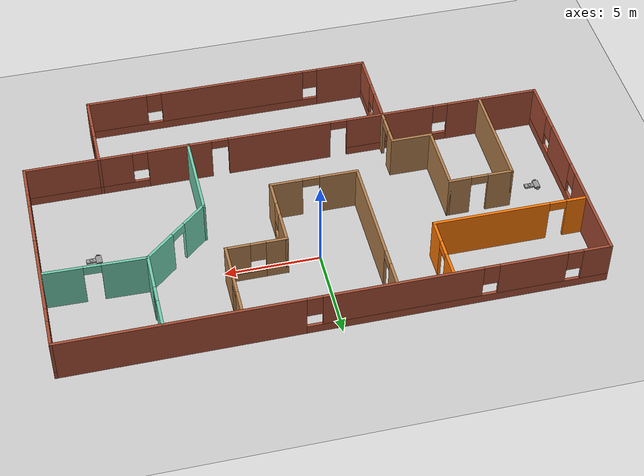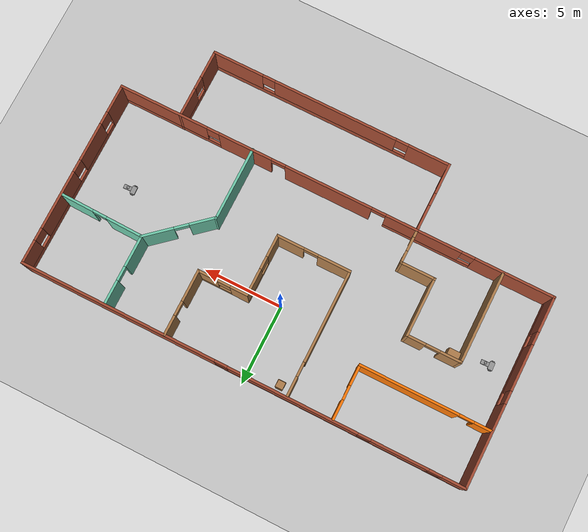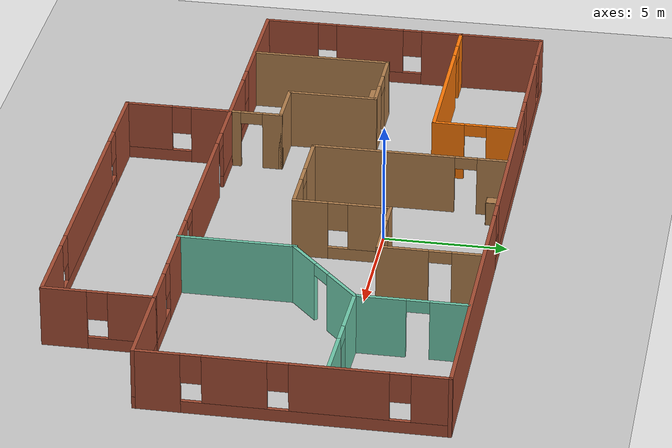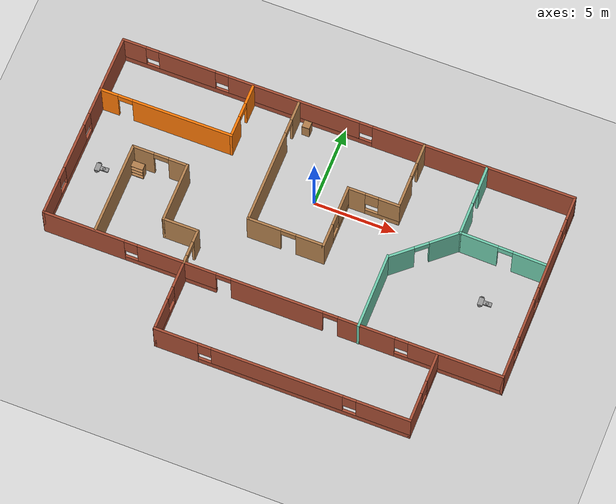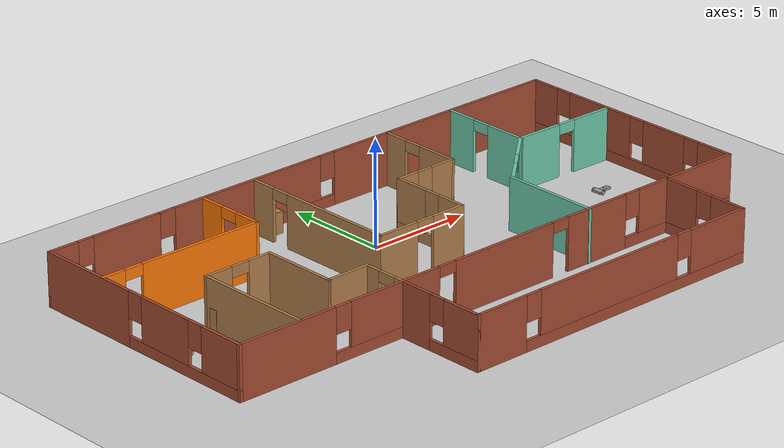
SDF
<sdf version="1.6">
 <world name="default">
  <plugin name="hello" filename="libhello.so"/>
  <light name="sun" type="directional">
   <pose>0 0 10 0 -0 0</pose>
   <diffuse>0.8 0.8 0.8 1</diffuse>
   <specular>0.2 0.2 0.2 1</specular>
   <attenuation>
    <range>1000</range>
    <constant>0.9</constant>
    <linear>0.01</linear>
    <quadratic>0.001</quadratic>
   </attenuation>
   <direction>-0.5 0.1 -0.9</direction>
  </light>
  <model name="ground_plane">
   <static>1</static>
   <link name="link">
    <collision name="collision">
     <geometry><plane><normal>0 0 1</normal><size>100 100</size></plane></geometry>
     <surface>
      <contact><collide_bitmask>65535</collide_bitmask></contact>
      <friction><ode><mu>100</mu><mu2>50</mu2></ode></friction>
     </surface>
    </collision>
    <visual name="visual">
     <cast_shadows>0</cast_shadows>
     <geometry><plane><normal>0 0 1</normal><size>100 100</size></plane></geometry>
     <material>
      <script><uri>file://media/materials/scripts/gazebo.material</uri><name>Gazebo/Grey</name></script>
     </material>
    </visual>
   </link>
  </model>
  <gravity>0 0 -9.8</gravity>
  <magnetic_field>6e-06 2.3e-05 -4.2e-05</magnetic_field>
  <atmosphere type="adiabatic"/>
  <physics name="default_physics" default="0" type="ode">
   <max_step_size>0.001</max_step_size>
   <real_time_factor>1</real_time_factor>
   <real_time_update_rate>1000</real_time_update_rate>
  </physics>
  <scene><ambient>0.4 0.4 0.4 1</ambient><background>0.7 0.7 0.7 1</background><shadows>1</shadows></scene>
  <spherical_coordinates>
   <surface_model>EARTH_WGS84</surface_model>
   <latitude_deg>0</latitude_deg>
   <longitude_deg>0</longitude_deg>
   <elevation>0</elevation>
   <heading_deg>0</heading_deg>
  </spherical_coordinates>
  <model name="Building">
   <pose>0.19679 -3.43922 0 0 -0 0</pose>
   <link name="Wall_10">
    <pose>11.1971 3.62387 0 0 0 -0.022081</pose>
    <visual name="Wall_10_Visual_0">
     <pose>-1.47859 0 1.25 0 -0 0</pose>
     <geometry><box><size>2.39049 0.15 2.5</size></box></geometry>
     <material>
      <script><uri>file://media/materials/scripts/gazebo.material</uri><name>Gazebo/Grey</name></script>
      <ambient>0.435294 0.796078 0.67451 1</ambient>
     </material>
     <meta><layer>0</layer></meta>
    </visual>
    <collision name="Wall_10_Collision_0">
     <geometry><box><size>2.39049 0.15 2.5</size></box></geometry>
     <pose>-1.47859 0 1.25 0 -0 0</pose>
    </collision>
    <visual name="Wall_10_Visual_1">
     <pose>1.64525 0 1.25 0 -0 0</pose>
     <geometry><box><size>2.05719 0.15 2.5</size></box></geometry>
     <material>
      <script><uri>file://media/materials/scripts/gazebo.material</uri><name>Gazebo/Grey</name></script>
      <ambient>0.435294 0.796078 0.67451 1</ambient>
     </material>
     <meta><layer>0</layer></meta>
    </visual>
    <collision name="Wall_10_Collision_1">
     <geometry><box><size>2.05719 0.15 2.5</size></box></geometry>
     <pose>1.64525 0 1.25 0 -0 0</pose>
    </collision>
    <visual name="Wall_10_Visual_2">
     <pose>0.166652 0 2.25 0 -0 0</pose>
     <geometry><box><size>0.9 0.15 0.5</size></box></geometry>
     <material>
      <script><uri>file://media/materials/scripts/gazebo.material</uri><name>Gazebo/Grey</name></script>
      <ambient>0.435294 0.796078 0.67451 1</ambient>
     </material>
     <meta><layer>0</layer></meta>
    </visual>
    <collision name="Wall_10_Collision_2">
     <geometry><box><size>0.9 0.15 0.5</size></box></geometry>
     <pose>0.166652 0 2.25 0 -0 0</pose>
    </collision>
   </link>
   <link name="Wall_12">
    <pose>8.59888 5.84302 0 0 -0 1.5708</pose>
    <visual name="Wall_12_Visual_0">
     <pose>-1.2176 0 1.25 0 -0 0</pose>
     <geometry><box><size>2.06481 0.15 2.5</size></box></geometry>
     <material>
      <script><uri>file://media/materials/scripts/gazebo.material</uri><name>Gazebo/Grey</name></script>
      <ambient>0.435294 0.796078 0.67451 1</ambient>
     </material>
     <meta><layer>0</layer></meta>
    </visual>
    <collision name="Wall_12_Collision_0">
     <geometry><box><size>2.06481 0.15 2.5</size></box></geometry>
     <pose>-1.2176 0 1.25 0 -0 0</pose>
    </collision>
    <visual name="Wall_12_Visual_1">
     <pose>1.4824 0 1.25 0 -0 0</pose>
     <geometry><box><size>1.53519 0.15 2.5</size></box></geometry>
     <material>
      <script><uri>file://media/materials/scripts/gazebo.material</uri><name>Gazebo/Grey</name></script>
      <ambient>0.435294 0.796078 0.67451 1</ambient>
     </material>
     <meta><layer>0</layer></meta>
    </visual>
    <collision name="Wall_12_Collision_1">
     <geometry><box><size>1.53519 0.15 2.5</size></box></geometry>
     <pose>1.4824 0 1.25 0 -0 0</pose>
    </collision>
    <visual name="Wall_12_Visual_2">
     <pose>0.264806 0 2.25 0 -0 0</pose>
     <geometry><box><size>0.9 0.15 0.5</size></box></geometry>
     <material>
      <script><uri>file://media/materials/scripts/gazebo.material</uri><name>Gazebo/Grey</name></script>
      <ambient>0.435294 0.796078 0.67451 1</ambient>
     </material>
     <meta><layer>0</layer></meta>
    </visual>
    <collision name="Wall_12_Collision_2">
     <geometry><box><size>0.9 0.15 0.5</size></box></geometry>
     <pose>0.264806 0 2.25 0 -0 0</pose>
    </collision>
   </link>
   <link name="Wall_14">
    <pose>-2.94311 4.05196 0 0 0 -1.5708</pose>
    <visual name="Wall_14_Visual_0">
     <pose>-3.37904 0 1.25 0 -0 0</pose>
     <geometry><box><size>1.24193 0.15 2.5</size></box></geometry>
     <material>
      <script><uri>file://media/materials/scripts/gazebo.material</uri><name>Gazebo/Wood</name></script>
      <ambient>1 1 1 1</ambient>
     </material>
     <meta><layer>0</layer></meta>
    </visual>
    <collision name="Wall_14_Collision_0">
     <geometry><box><size>1.24193 0.15 2.5</size></box></geometry>
     <pose>-3.37904 0 1.25 0 -0 0</pose>
    </collision>
    <visual name="Wall_14_Visual_1">
     <pose>1.07096 0 1.25 0 -0 0</pose>
     <geometry><box><size>5.85807 0.15 2.5</size></box></geometry>
     <material>
      <script><uri>file://media/materials/scripts/gazebo.material</uri><name>Gazebo/Wood</name></script>
      <ambient>1 1 1 1</ambient>
     </material>
     <meta><layer>0</layer></meta>
    </visual>
    <collision name="Wall_14_Collision_1">
     <geometry><box><size>5.85807 0.15 2.5</size></box></geometry>
     <pose>1.07096 0 1.25 0 -0 0</pose>
    </collision>
    <visual name="Wall_14_Visual_2">
     <pose>-2.30807 0 2.25 0 -0 0</pose>
     <geometry><box><size>0.9 0.15 0.5</size></box></geometry>
     <material>
      <script><uri>file://media/materials/scripts/gazebo.material</uri><name>Gazebo/Wood</name></script>
      <ambient>1 1 1 1</ambient>
     </material>
     <meta><layer>0</layer></meta>
    </visual>
    <collision name="Wall_14_Collision_2">
     <geometry><box><size>0.9 0.15 0.5</size></box></geometry>
     <pose>-2.30807 0 2.25 0 -0 0</pose>
    </collision>
   </link>
   <link name="Wall_15">
    <pose>-0.643108 0.126957 0 0 -0 0</pose>
    <visual name="Wall_15_Visual_0">
     <pose>-1.33137 0 1.25 0 -0 0</pose>
     <geometry><box><size>2.08726 0.15 2.5</size></box></geometry>
     <material>
      <script><uri>file://media/materials/scripts/gazebo.material</uri><name>Gazebo/Wood</name></script>
      <ambient>1 1 1 1</ambient>
     </material>
     <meta><layer>0</layer></meta>
    </visual>
    <collision name="Wall_15_Collision_0">
     <geometry><box><size>2.08726 0.15 2.5</size></box></geometry>
     <pose>-1.33137 0 1.25 0 -0 0</pose>
    </collision>
    <visual name="Wall_15_Visual_1">
     <pose>1.49363 0 1.25 0 -0 0</pose>
     <geometry><box><size>1.76274 0.15 2.5</size></box></geometry>
     <material>
      <script><uri>file://media/materials/scripts/gazebo.material</uri><name>Gazebo/Wood</name></script>
      <ambient>1 1 1 1</ambient>
     </material>
     <meta><layer>0</layer></meta>
    </visual>
    <collision name="Wall_15_Collision_1">
     <geometry><box><size>1.76274 0.15 2.5</size></box></geometry>
     <pose>1.49363 0 1.25 0 -0 0</pose>
    </collision>
    <visual name="Wall_15_Visual_2">
     <pose>0.16226 0 2.25 0 -0 0</pose>
     <geometry><box><size>0.9 0.15 0.5</size></box></geometry>
     <material>
      <script><uri>file://media/materials/scripts/gazebo.material</uri><name>Gazebo/Wood</name></script>
      <ambient>1 1 1 1</ambient>
     </material>
     <meta><layer>0</layer></meta>
    </visual>
    <collision name="Wall_15_Collision_2">
     <geometry><box><size>0.9 0.15 0.5</size></box></geometry>
     <pose>0.16226 0 2.25 0 -0 0</pose>
    </collision>
   </link>
   <link name="Wall_16">
    <pose>1.65689 2.05196 0 0 -0 1.5708</pose>
    <visual name="Wall_16_Visual_0">
     <pose>-1.27857 0 1.25 0 -0 0</pose>
     <geometry><box><size>1.44286 0.15 2.5</size></box></geometry>
     <material>
      <script><uri>file://media/materials/scripts/gazebo.material</uri><name>Gazebo/Wood</name></script>
      <ambient>1 1 1 1</ambient>
     </material>
     <meta><layer>0</layer></meta>
    </visual>
    <collision name="Wall_16_Collision_0">
     <geometry><box><size>1.44286 0.15 2.5</size></box></geometry>
     <pose>-1.27857 0 1.25 0 -0 0</pose>
    </collision>
    <visual name="Wall_16_Visual_1">
     <pose>0.721429 0 0.25 0 -0 0</pose>
     <geometry><box><size>2.55714 0.15 0.5</size></box></geometry>
     <material>
      <script><uri>file://media/materials/scripts/gazebo.material</uri><name>Gazebo/Wood</name></script>
      <ambient>1 1 1 1</ambient>
     </material>
     <meta><layer>0</layer></meta>
    </visual>
    <collision name="Wall_16_Collision_1">
     <geometry><box><size>2.55714 0.15 0.5</size></box></geometry>
     <pose>0.721429 0 0.25 0 -0 0</pose>
    </collision>
    <visual name="Wall_16_Visual_2">
     <pose>1.12143 0 1.5 0 -0 0</pose>
     <geometry><box><size>1.75714 0.15 2</size></box></geometry>
     <material>
      <script><uri>file://media/materials/scripts/gazebo.material</uri><name>Gazebo/Wood</name></script>
      <ambient>1 1 1 1</ambient>
     </material>
     <meta><layer>0</layer></meta>
    </visual>
    <collision name="Wall_16_Collision_2">
     <geometry><box><size>1.75714 0.15 2</size></box></geometry>
     <pose>1.12143 0 1.5 0 -0 0</pose>
    </collision>
    <visual name="Wall_16_Visual_3">
     <pose>-0.157143 0 1.9 0 -0 0</pose>
     <geometry><box><size>0.8 0.15 1.2</size></box></geometry>
     <material>
      <script><uri>file://media/materials/scripts/gazebo.material</uri><name>Gazebo/Wood</name></script>
      <ambient>1 1 1 1</ambient>
     </material>
     <meta><layer>0</layer></meta>
    </visual>
    <collision name="Wall_16_Collision_3">
     <geometry><box><size>0.8 0.15 1.2</size></box></geometry>
     <pose>-0.157143 0 1.9 0 -0 0</pose>
    </collision>
   </link>
   <link name="Wall_17">
    <pose>3.20689 3.97696 0 0 -0 0</pose>
    <visual name="Wall_17_Visual_0">
     <pose>-1.05597 0 1.25 0 -0 0</pose>
     <geometry><box><size>1.13807 0.15 2.5</size></box></geometry>
     <material>
      <script><uri>file://media/materials/scripts/gazebo.material</uri><name>Gazebo/Wood</name></script>
      <ambient>1 1 1 1</ambient>
     </material>
     <meta><layer>0</layer></meta>
    </visual>
    <collision name="Wall_17_Collision_0">
     <geometry><box><size>1.13807 0.15 2.5</size></box></geometry>
     <pose>-1.05597 0 1.25 0 -0 0</pose>
    </collision>
    <visual name="Wall_17_Visual_1">
     <pose>0.569033 0 0.25 0 -0 0</pose>
     <geometry><box><size>2.11193 0.15 0.5</size></box></geometry>
     <material>
      <script><uri>file://media/materials/scripts/gazebo.material</uri><name>Gazebo/Wood</name></script>
      <ambient>1 1 1 1</ambient>
     </material>
     <meta><layer>0</layer></meta>
    </visual>
    <collision name="Wall_17_Collision_1">
     <geometry><box><size>2.11193 0.15 0.5</size></box></geometry>
     <pose>0.569033 0 0.25 0 -0 0</pose>
    </collision>
    <visual name="Wall_17_Visual_2">
     <pose>0.969033 0 1.5 0 -0 0</pose>
     <geometry><box><size>1.31193 0.15 2</size></box></geometry>
     <material>
      <script><uri>file://media/materials/scripts/gazebo.material</uri><name>Gazebo/Wood</name></script>
      <ambient>1 1 1 1</ambient>
     </material>
     <meta><layer>0</layer></meta>
    </visual>
    <collision name="Wall_17_Collision_2">
     <geometry><box><size>1.31193 0.15 2</size></box></geometry>
     <pose>0.969033 0 1.5 0 -0 0</pose>
    </collision>
    <visual name="Wall_17_Visual_3">
     <pose>-0.086934 0 1.9 0 -0 0</pose>
     <geometry><box><size>0.8 0.15 1.2</size></box></geometry>
     <material>
      <script><uri>file://media/materials/scripts/gazebo.material</uri><name>Gazebo/Wood</name></script>
      <ambient>1 1 1 1</ambient>
     </material>
     <meta><layer>0</layer></meta>
    </visual>
    <collision name="Wall_17_Collision_3">
     <geometry><box><size>0.8 0.15 1.2</size></box></geometry>
     <pose>-0.086934 0 1.9 0 -0 0</pose>
    </collision>
   </link>
   <link name="Wall_18">
    <pose>4.75689 6.02696 0 0 -0 1.5708</pose>
    <visual name="Wall_18_Visual_0">
     <pose>-1.09849 0 1.25 0 -0 0</pose>
     <geometry><box><size>2.05302 0.15 2.5</size></box></geometry>
     <material>
      <script><uri>file://media/materials/scripts/gazebo.material</uri><name>Gazebo/Wood</name></script>
      <ambient>1 1 1 1</ambient>
     </material>
     <meta><layer>0</layer></meta>
    </visual>
    <collision name="Wall_18_Collision_0">
     <geometry><box><size>2.05302 0.15 2.5</size></box></geometry>
     <pose>-1.09849 0 1.25 0 -0 0</pose>
    </collision>
    <visual name="Wall_18_Visual_1">
     <pose>1.47651 0 1.25 0 -0 0</pose>
     <geometry><box><size>1.29698 0.15 2.5</size></box></geometry>
     <material>
      <script><uri>file://media/materials/scripts/gazebo.material</uri><name>Gazebo/Wood</name></script>
      <ambient>1 1 1 1</ambient>
     </material>
     <meta><layer>0</layer></meta>
    </visual>
    <collision name="Wall_18_Collision_1">
     <geometry><box><size>1.29698 0.15 2.5</size></box></geometry>
     <pose>1.47651 0 1.25 0 -0 0</pose>
    </collision>
    <visual name="Wall_18_Visual_2">
     <pose>0.378016 0 2.25 0 -0 0</pose>
     <geometry><box><size>0.9 0.15 0.5</size></box></geometry>
     <material>
      <script><uri>file://media/materials/scripts/gazebo.material</uri><name>Gazebo/Wood</name></script>
      <ambient>1 1 1 1</ambient>
     </material>
     <meta><layer>0</layer></meta>
    </visual>
    <collision name="Wall_18_Collision_2">
     <geometry><box><size>0.9 0.15 0.5</size></box></geometry>
     <pose>0.378016 0 2.25 0 -0 0</pose>
    </collision>
   </link>
   <link name="Wall_24">
    <collision name="Wall_24_Collision">
     <geometry><box><size>5.75 0.15 2.5</size></box></geometry>
     <pose>0 0 1.25 0 -0 0</pose>
    </collision>
    <visual name="Wall_24_Visual">
     <pose>0 0 1.25 0 -0 0</pose>
     <geometry><box><size>5.75 0.15 2.5</size></box></geometry>
     <material>
      <script><uri>file://media/materials/scripts/gazebo.material</uri><name>Gazebo/Wood</name></script>
      <ambient>1 1 1 1</ambient>
     </material>
     <meta><layer>0</layer></meta>
    </visual>
    <pose>-10.7742 -0.849319 0 0 0 -1.5708</pose>
   </link>
   <link name="Wall_26">
    <pose>-9.09921 1.95068 0 0 -0 0</pose>
    <visual name="Wall_26_Visual_0">
     <pose>-1.06472 0 1.25 0 -0 0</pose>
     <geometry><box><size>1.37057 0.15 2.5</size></box></geometry>
     <material>
      <script><uri>file://media/materials/scripts/gazebo.material</uri><name>Gazebo/Wood</name></script>
      <ambient>1 1 1 1</ambient>
     </material>
     <meta><layer>0</layer></meta>
    </visual>
    <collision name="Wall_26_Collision_0">
     <geometry><box><size>1.37057 0.15 2.5</size></box></geometry>
     <pose>-1.06472 0 1.25 0 -0 0</pose>
    </collision>
    <visual name="Wall_26_Visual_1">
     <pose>1.13528 0 1.25 0 -0 0</pose>
     <geometry><box><size>1.22943 0.15 2.5</size></box></geometry>
     <material>
      <script><uri>file://media/materials/scripts/gazebo.material</uri><name>Gazebo/Wood</name></script>
      <ambient>1 1 1 1</ambient>
     </material>
     <meta><layer>0</layer></meta>
    </visual>
    <collision name="Wall_26_Collision_1">
     <geometry><box><size>1.22943 0.15 2.5</size></box></geometry>
     <pose>1.13528 0 1.25 0 -0 0</pose>
    </collision>
    <visual name="Wall_26_Visual_2">
     <pose>0.070568 0 2.25 0 -0 0</pose>
     <geometry><box><size>0.9 0.15 0.5</size></box></geometry>
     <material>
      <script><uri>file://media/materials/scripts/gazebo.material</uri><name>Gazebo/Wood</name></script>
      <ambient>1 1 1 1</ambient>
     </material>
     <meta><layer>0</layer></meta>
    </visual>
    <collision name="Wall_26_Collision_2">
     <geometry><box><size>0.9 0.15 0.5</size></box></geometry>
     <pose>0.070568 0 2.25 0 -0 0</pose>
    </collision>
   </link>
   <link name="Wall_27">
    <collision name="Wall_27_Collision">
     <geometry><box><size>3.75 0.15 2.5</size></box></geometry>
     <pose>0 0 1.25 0 -0 0</pose>
    </collision>
    <visual name="Wall_27_Visual">
     <pose>0 0 1.25 0 -0 0</pose>
     <geometry><box><size>3.75 0.15 2.5</size></box></geometry>
     <material>
      <script><uri>file://media/materials/scripts/gazebo.material</uri><name>Gazebo/Wood</name></script>
      <ambient>1 1 1 1</ambient>
     </material>
     <meta><layer>0</layer></meta>
    </visual>
    <pose>-7.42421 0.150682 0 0 0 -1.5708</pose>
   </link>
   <link name="Wall_3">
    <pose>0 8.09932 0 0 -0 3.14159</pose>
    <visual name="Wall_3_Visual_0">
     <pose>-7.78887 0 1.25 0 -0 0</pose>
     <geometry><box><size>12.4223 0.15 2.5</size></box></geometry>
     <material>
      <script><uri>file://media/materials/scripts/gazebo.material</uri><name>Gazebo/Bricks</name></script>
      <ambient>1 1 1 1</ambient>
     </material>
     <meta><layer>0</layer></meta>
    </visual>
    <collision name="Wall_3_Collision_0">
     <geometry><box><size>12.4223 0.15 2.5</size></box></geometry>
     <pose>-7.78887 0 1.25 0 -0 0</pose>
    </collision>
    <visual name="Wall_3_Visual_1">
     <pose>6.21113 0 0.25 0 -0 0</pose>
     <geometry><box><size>15.5777 0.15 0.5</size></box></geometry>
     <material>
      <script><uri>file://media/materials/scripts/gazebo.material</uri><name>Gazebo/Bricks</name></script>
      <ambient>1 1 1 1</ambient>
     </material>
     <meta><layer>0</layer></meta>
    </visual>
    <collision name="Wall_3_Collision_1">
     <geometry><box><size>15.5777 0.15 0.5</size></box></geometry>
     <pose>6.21113 0 0.25 0 -0 0</pose>
    </collision>
    <visual name="Wall_3_Visual_2">
     <pose>3.28973 0 1.5 0 -0 0</pose>
     <geometry><box><size>8.13492 0.15 2</size></box></geometry>
     <material>
      <script><uri>file://media/materials/scripts/gazebo.material</uri><name>Gazebo/Bricks</name></script>
      <ambient>1 1 1 1</ambient>
     </material>
     <meta><layer>0</layer></meta>
    </visual>
    <collision name="Wall_3_Collision_2">
     <geometry><box><size>8.13492 0.15 2</size></box></geometry>
     <pose>3.28973 0 1.5 0 -0 0</pose>
    </collision>
    <visual name="Wall_3_Visual_3">
     <pose>9.92404 0 1.5 0 -0 0</pose>
     <geometry><box><size>3.5337 0.15 2</size></box></geometry>
     <material>
      <script><uri>file://media/materials/scripts/gazebo.material</uri><name>Gazebo/Bricks</name></script>
      <ambient>1 1 1 1</ambient>
     </material>
     <meta><layer>0</layer></meta>
    </visual>
    <collision name="Wall_3_Collision_3">
     <geometry><box><size>3.5337 0.15 2</size></box></geometry>
     <pose>9.92404 0 1.5 0 -0 0</pose>
    </collision>
    <visual name="Wall_3_Visual_4">
     <pose>13.2454 0 1.5 0 -0 0</pose>
     <geometry><box><size>1.50911 0.15 2</size></box></geometry>
     <material>
      <script><uri>file://media/materials/scripts/gazebo.material</uri><name>Gazebo/Bricks</name></script>
      <ambient>1 1 1 1</ambient>
     </material>
     <meta><layer>0</layer></meta>
    </visual>
    <collision name="Wall_3_Collision_4">
     <geometry><box><size>1.50911 0.15 2</size></box></geometry>
     <pose>13.2454 0 1.5 0 -0 0</pose>
    </collision>
    <visual name="Wall_3_Visual_5">
     <pose>-1.17773 0 1.9 0 -0 0</pose>
     <geometry><box><size>0.8 0.15 1.2</size></box></geometry>
     <material>
      <script><uri>file://media/materials/scripts/gazebo.material</uri><name>Gazebo/Bricks</name></script>
      <ambient>1 1 1 1</ambient>
     </material>
     <meta><layer>0</layer></meta>
    </visual>
    <collision name="Wall_3_Collision_5">
     <geometry><box><size>0.8 0.15 1.2</size></box></geometry>
     <pose>-1.17773 0 1.9 0 -0 0</pose>
    </collision>
    <visual name="Wall_3_Visual_6">
     <pose>7.75719 0 1.9 0 -0 0</pose>
     <geometry><box><size>0.8 0.15 1.2</size></box></geometry>
     <material>
      <script><uri>file://media/materials/scripts/gazebo.material</uri><name>Gazebo/Bricks</name></script>
      <ambient>1 1 1 1</ambient>
     </material>
     <meta><layer>0</layer></meta>
    </visual>
    <collision name="Wall_3_Collision_6">
     <geometry><box><size>0.8 0.15 1.2</size></box></geometry>
     <pose>7.75719 0 1.9 0 -0 0</pose>
    </collision>
    <visual name="Wall_3_Visual_7">
     <pose>12.0909 0 1.9 0 -0 0</pose>
     <geometry><box><size>0.8 0.15 1.2</size></box></geometry>
     <material>
      <script><uri>file://media/materials/scripts/gazebo.material</uri><name>Gazebo/Bricks</name></script>
      <ambient>1 1 1 1</ambient>
     </material>
     <meta><layer>0</layer></meta>
    </visual>
    <collision name="Wall_3_Collision_7">
     <geometry><box><size>0.8 0.15 1.2</size></box></geometry>
     <pose>12.0909 0 1.9 0 -0 0</pose>
    </collision>
   </link>
   <link name="Wall_31">
    <collision name="Wall_31_Collision">
     <geometry><box><size>2.25 0.15 2.5</size></box></geometry>
     <pose>0 0 1.25 0 -0 0</pose>
    </collision>
    <visual name="Wall_31_Visual">
     <pose>0 0 1.25 0 -0 0</pose>
     <geometry><box><size>2.25 0.15 2.5</size></box></geometry>
     <material>
      <script><uri>file://media/materials/scripts/gazebo.material</uri><name>Gazebo/Wood</name></script>
      <ambient>1 1 1 1</ambient>
     </material>
     <meta><layer>0</layer></meta>
    </visual>
    <pose>-6.37421 -1.64932 0 0 -0 0</pose>
   </link>
   <link name="Wall_32">
    <pose>-5.32421 -2.69932 0 0 0 -1.5708</pose>
    <visual name="Wall_32_Visual_0">
     <pose>-0.711165 0 1.25 0 -0 0</pose>
     <geometry><box><size>0.827671 0.15 2.5</size></box></geometry>
     <material>
      <script><uri>file://media/materials/scripts/gazebo.material</uri><name>Gazebo/Wood</name></script>
      <ambient>1 1 1 1</ambient>
     </material>
     <meta><layer>0</layer></meta>
    </visual>
    <collision name="Wall_32_Collision_0">
     <geometry><box><size>0.827671 0.15 2.5</size></box></geometry>
     <pose>-0.711165 0 1.25 0 -0 0</pose>
    </collision>
    <visual name="Wall_32_Visual_1">
     <pose>0.863835 0 1.25 0 -0 0</pose>
     <geometry><box><size>0.522329 0.15 2.5</size></box></geometry>
     <material>
      <script><uri>file://media/materials/scripts/gazebo.material</uri><name>Gazebo/Wood</name></script>
      <ambient>1 1 1 1</ambient>
     </material>
     <meta><layer>0</layer></meta>
    </visual>
    <collision name="Wall_32_Collision_1">
     <geometry><box><size>0.522329 0.15 2.5</size></box></geometry>
     <pose>0.863835 0 1.25 0 -0 0</pose>
    </collision>
    <visual name="Wall_32_Visual_2">
     <pose>0.152671 0 2.25 0 -0 0</pose>
     <geometry><box><size>0.9 0.15 0.5</size></box></geometry>
     <material>
      <script><uri>file://media/materials/scripts/gazebo.material</uri><name>Gazebo/Wood</name></script>
      <ambient>1 1 1 1</ambient>
     </material>
     <meta><layer>0</layer></meta>
    </visual>
    <collision name="Wall_32_Collision_2">
     <geometry><box><size>0.9 0.15 0.5</size></box></geometry>
     <pose>0.152671 0 2.25 0 -0 0</pose>
    </collision>
   </link>
   <link name="Wall_34">
    <pose>-13.925 2.17432 0 0 0 -1.5708</pose>
    <visual name="Wall_34_Visual_0">
     <pose>-3.38924 0 1.25 0 -0 0</pose>
     <geometry><box><size>5.22152 0.15 2.5</size></box></geometry>
     <material>
      <script><uri>file://media/materials/scripts/gazebo.material</uri><name>Gazebo/Bricks</name></script>
      <ambient>1 1 1 1</ambient>
     </material>
     <meta><layer>0</layer></meta>
    </visual>
    <collision name="Wall_34_Collision_0">
     <geometry><box><size>5.22152 0.15 2.5</size></box></geometry>
     <pose>-3.38924 0 1.25 0 -0 0</pose>
    </collision>
    <visual name="Wall_34_Visual_1">
     <pose>2.61076 0 0.25 0 -0 0</pose>
     <geometry><box><size>6.77848 0.15 0.5</size></box></geometry>
     <material>
      <script><uri>file://media/materials/scripts/gazebo.material</uri><name>Gazebo/Bricks</name></script>
      <ambient>1 1 1 1</ambient>
     </material>
     <meta><layer>0</layer></meta>
    </visual>
    <collision name="Wall_34_Collision_1">
     <geometry><box><size>6.77848 0.15 0.5</size></box></geometry>
     <pose>2.61076 0 0.25 0 -0 0</pose>
    </collision>
    <visual name="Wall_34_Visual_2">
     <pose>1.46736 0 1.5 0 -0 0</pose>
     <geometry><box><size>2.89167 0.15 2</size></box></geometry>
     <material>
      <script><uri>file://media/materials/scripts/gazebo.material</uri><name>Gazebo/Bricks</name></script>
      <ambient>1 1 1 1</ambient>
     </material>
     <meta><layer>0</layer></meta>
    </visual>
    <collision name="Wall_34_Collision_2">
     <geometry><box><size>2.89167 0.15 2</size></box></geometry>
     <pose>1.46736 0 1.5 0 -0 0</pose>
    </collision>
    <visual name="Wall_34_Visual_3">
     <pose>4.8566 0 1.5 0 -0 0</pose>
     <geometry><box><size>2.2868 0.15 2</size></box></geometry>
     <material>
      <script><uri>file://media/materials/scripts/gazebo.material</uri><name>Gazebo/Bricks</name></script>
      <ambient>1 1 1 1</ambient>
     </material>
     <meta><layer>0</layer></meta>
    </visual>
    <collision name="Wall_34_Collision_3">
     <geometry><box><size>2.2868 0.15 2</size></box></geometry>
     <pose>4.8566 0 1.5 0 -0 0</pose>
    </collision>
    <visual name="Wall_34_Visual_4">
     <pose>-0.378475 0 1.9 0 -0 0</pose>
     <geometry><box><size>0.8 0.15 1.2</size></box></geometry>
     <material>
      <script><uri>file://media/materials/scripts/gazebo.material</uri><name>Gazebo/Bricks</name></script>
      <ambient>1 1 1 1</ambient>
     </material>
     <meta><layer>0</layer></meta>
    </visual>
    <collision name="Wall_34_Collision_4">
     <geometry><box><size>0.8 0.15 1.2</size></box></geometry>
     <pose>-0.378475 0 1.9 0 -0 0</pose>
    </collision>
    <visual name="Wall_34_Visual_5">
     <pose>3.3132 0 1.9 0 -0 0</pose>
     <geometry><box><size>0.8 0.15 1.2</size></box></geometry>
     <material>
      <script><uri>file://media/materials/scripts/gazebo.material</uri><name>Gazebo/Bricks</name></script>
      <ambient>1 1 1 1</ambient>
     </material>
     <meta><layer>0</layer></meta>
    </visual>
    <collision name="Wall_34_Collision_5">
     <geometry><box><size>0.8 0.15 1.2</size></box></geometry>
     <pose>3.3132 0 1.9 0 -0 0</pose>
    </collision>
   </link>
   <link name="Wall_35">
    <pose>0 -3.75068 0 0 -0 0</pose>
    <visual name="Wall_35_Visual_0">
     <pose>-11.4799 0 1.25 0 -0 0</pose>
     <geometry><box><size>5.04027 0.15 2.5</size></box></geometry>
     <material>
      <script><uri>file://media/materials/scripts/gazebo.material</uri><name>Gazebo/Bricks</name></script>
      <ambient>1 1 1 1</ambient>
     </material>
     <meta><layer>0</layer></meta>
    </visual>
    <collision name="Wall_35_Collision_0">
     <geometry><box><size>5.04027 0.15 2.5</size></box></geometry>
     <pose>-11.4799 0 1.25 0 -0 0</pose>
    </collision>
    <visual name="Wall_35_Visual_1">
     <pose>0.344575 0 1.25 0 -0 0</pose>
     <geometry><box><size>5.57657 0.15 2.5</size></box></geometry>
     <material>
      <script><uri>file://media/materials/scripts/gazebo.material</uri><name>Gazebo/Bricks</name></script>
      <ambient>1 1 1 1</ambient>
     </material>
     <meta><layer>0</layer></meta>
    </visual>
    <collision name="Wall_35_Collision_1">
     <geometry><box><size>5.57657 0.15 2.5</size></box></geometry>
     <pose>0.344575 0 1.25 0 -0 0</pose>
    </collision>
    <visual name="Wall_35_Visual_2">
     <pose>5.7492 0 1.25 0 -0 0</pose>
     <geometry><box><size>3.43268 0.15 2.5</size></box></geometry>
     <material>
      <script><uri>file://media/materials/scripts/gazebo.material</uri><name>Gazebo/Bricks</name></script>
      <ambient>1 1 1 1</ambient>
     </material>
     <meta><layer>0</layer></meta>
    </visual>
    <collision name="Wall_35_Collision_2">
     <geometry><box><size>3.43268 0.15 2.5</size></box></geometry>
     <pose>5.7492 0 1.25 0 -0 0</pose>
    </collision>
    <visual name="Wall_35_Visual_3">
     <pose>-6.15172 0 0.25 0 -0 0</pose>
     <geometry><box><size>5.61601 0.15 0.5</size></box></geometry>
     <material>
      <script><uri>file://media/materials/scripts/gazebo.material</uri><name>Gazebo/Bricks</name></script>
      <ambient>1 1 1 1</ambient>
     </material>
     <meta><layer>0</layer></meta>
    </visual>
    <collision name="Wall_35_Collision_3">
     <geometry><box><size>5.61601 0.15 0.5</size></box></geometry>
     <pose>-6.15172 0 0.25 0 -0 0</pose>
    </collision>
    <visual name="Wall_35_Visual_4">
     <pose>10.7328 0 0.25 0 -0 0</pose>
     <geometry><box><size>6.53446 0.15 0.5</size></box></geometry>
     <material>
      <script><uri>file://media/materials/scripts/gazebo.material</uri><name>Gazebo/Bricks</name></script>
      <ambient>1 1 1 1</ambient>
     </material>
     <meta><layer>0</layer></meta>
    </visual>
    <collision name="Wall_35_Collision_4">
     <geometry><box><size>6.53446 0.15 0.5</size></box></geometry>
     <pose>10.7328 0 0.25 0 -0 0</pose>
    </collision>
    <visual name="Wall_35_Visual_5">
     <pose>-5.75172 0 1.5 0 -0 0</pose>
     <geometry><box><size>4.81602 0.15 2</size></box></geometry>
     <material>
      <script><uri>file://media/materials/scripts/gazebo.material</uri><name>Gazebo/Bricks</name></script>
      <ambient>1 1 1 1</ambient>
     </material>
     <meta><layer>0</layer></meta>
    </visual>
    <collision name="Wall_35_Collision_5">
     <geometry><box><size>4.81602 0.15 2</size></box></geometry>
     <pose>-5.75172 0 1.5 0 -0 0</pose>
    </collision>
    <visual name="Wall_35_Visual_6">
     <pose>-5.75172 0 1.5 0 -0 0</pose>
     <geometry><box><size>4.81602 0.15 2</size></box></geometry>
     <material>
      <script><uri>file://media/materials/scripts/gazebo.material</uri><name>Gazebo/Bricks</name></script>
      <ambient>1 1 1 1</ambient>
     </material>
     <meta><layer>0</layer></meta>
    </visual>
    <collision name="Wall_35_Collision_6">
     <geometry><box><size>4.81602 0.15 2</size></box></geometry>
     <pose>-5.75172 0 1.5 0 -0 0</pose>
    </collision>
    <visual name="Wall_35_Visual_7">
     <pose>11.1328 0 1.5 0 -0 0</pose>
     <geometry><box><size>5.73446 0.15 2</size></box></geometry>
     <material>
      <script><uri>file://media/materials/scripts/gazebo.material</uri><name>Gazebo/Bricks</name></script>
      <ambient>1 1 1 1</ambient>
     </material>
     <meta><layer>0</layer></meta>
    </visual>
    <collision name="Wall_35_Collision_7">
     <geometry><box><size>5.73446 0.15 2</size></box></geometry>
     <pose>11.1328 0 1.5 0 -0 0</pose>
    </collision>
    <visual name="Wall_35_Visual_8">
     <pose>-8.55973 0 1.9 0 -0 0</pose>
     <geometry><box><size>0.8 0.15 1.2</size></box></geometry>
     <material>
      <script><uri>file://media/materials/scripts/gazebo.material</uri><name>Gazebo/Bricks</name></script>
      <ambient>1 1 1 1</ambient>
     </material>
     <meta><layer>0</layer></meta>
    </visual>
    <collision name="Wall_35_Collision_8">
     <geometry><box><size>0.8 0.15 1.2</size></box></geometry>
     <pose>-8.55973 0 1.9 0 -0 0</pose>
    </collision>
    <visual name="Wall_35_Visual_9">
     <pose>7.86554 0 1.9 0 -0 0</pose>
     <geometry><box><size>0.8 0.15 1.2</size></box></geometry>
     <material>
      <script><uri>file://media/materials/scripts/gazebo.material</uri><name>Gazebo/Bricks</name></script>
      <ambient>1 1 1 1</ambient>
     </material>
     <meta><layer>0</layer></meta>
    </visual>
    <collision name="Wall_35_Collision_9">
     <geometry><box><size>0.8 0.15 1.2</size></box></geometry>
     <pose>7.86554 0 1.9 0 -0 0</pose>
    </collision>
    <visual name="Wall_35_Visual_10">
     <pose>3.58286 0 2.25 0 -0 0</pose>
     <geometry><box><size>0.9 0.15 0.5</size></box></geometry>
     <material>
      <script><uri>file://media/materials/scripts/gazebo.material</uri><name>Gazebo/Bricks</name></script>
      <ambient>1 1 1 1</ambient>
     </material>
     <meta><layer>0</layer></meta>
    </visual>
    <collision name="Wall_35_Collision_10">
     <geometry><box><size>0.9 0.15 0.5</size></box></geometry>
     <pose>3.58286 0 2.25 0 -0 0</pose>
    </collision>
    <visual name="Wall_35_Visual_11">
     <pose>-2.89371 0 2.25 0 -0 0</pose>
     <geometry><box><size>0.9 0.15 0.5</size></box></geometry>
     <material>
      <script><uri>file://media/materials/scripts/gazebo.material</uri><name>Gazebo/Bricks</name></script>
      <ambient>1 1 1 1</ambient>
     </material>
     <meta><layer>0</layer></meta>
    </visual>
    <collision name="Wall_35_Collision_11">
     <geometry><box><size>0.9 0.15 0.5</size></box></geometry>
     <pose>-2.89371 0 2.25 0 -0 0</pose>
    </collision>
    <visual name="Wall_35_Visual_12">
     <pose>-2.89371 0 2.25 0 -0 0</pose>
     <geometry><box><size>0.9 0.15 0.5</size></box></geometry>
     <material>
      <script><uri>file://media/materials/scripts/gazebo.material</uri><name>Gazebo/Bricks</name></script>
      <ambient>1 1 1 1</ambient>
     </material>
     <meta><layer>0</layer></meta>
    </visual>
    <collision name="Wall_35_Collision_12">
     <geometry><box><size>0.9 0.15 0.5</size></box></geometry>
     <pose>-2.89371 0 2.25 0 -0 0</pose>
    </collision>
   </link>
   <link name="Wall_36">
    <pose>13.925 2.17432 0 0 -0 1.5708</pose>
    <visual name="Wall_36_Visual_0">
     <pose>-5.07061 0 1.25 0 -0 0</pose>
     <geometry><box><size>1.85878 0.15 2.5</size></box></geometry>
     <material>
      <script><uri>file://media/materials/scripts/gazebo.material</uri><name>Gazebo/Bricks</name></script>
      <ambient>1 1 1 1</ambient>
     </material>
     <meta><layer>0</layer></meta>
    </visual>
    <collision name="Wall_36_Collision_0">
     <geometry><box><size>1.85878 0.15 2.5</size></box></geometry>
     <pose>-5.07061 0 1.25 0 -0 0</pose>
    </collision>
    <visual name="Wall_36_Visual_1">
     <pose>0.929391 0 0.25 0 -0 0</pose>
     <geometry><box><size>10.1412 0.15 0.5</size></box></geometry>
     <material>
      <script><uri>file://media/materials/scripts/gazebo.material</uri><name>Gazebo/Bricks</name></script>
      <ambient>1 1 1 1</ambient>
     </material>
     <meta><layer>0</layer></meta>
    </visual>
    <collision name="Wall_36_Collision_1">
     <geometry><box><size>10.1412 0.15 0.5</size></box></geometry>
     <pose>0.929391 0 0.25 0 -0 0</pose>
    </collision>
    <visual name="Wall_36_Visual_2">
     <pose>-2.10939 0 1.5 0 -0 0</pose>
     <geometry><box><size>2.46365 0.15 2</size></box></geometry>
     <material>
      <script><uri>file://media/materials/scripts/gazebo.material</uri><name>Gazebo/Bricks</name></script>
      <ambient>1 1 1 1</ambient>
     </material>
     <meta><layer>0</layer></meta>
    </visual>
    <collision name="Wall_36_Collision_2">
     <geometry><box><size>2.46365 0.15 2</size></box></geometry>
     <pose>-2.10939 0 1.5 0 -0 0</pose>
    </collision>
    <visual name="Wall_36_Visual_3">
     <pose>1.79629 0 1.5 0 -0 0</pose>
     <geometry><box><size>3.74771 0.15 2</size></box></geometry>
     <material>
      <script><uri>file://media/materials/scripts/gazebo.material</uri><name>Gazebo/Bricks</name></script>
      <ambient>1 1 1 1</ambient>
     </material>
     <meta><layer>0</layer></meta>
    </visual>
    <collision name="Wall_36_Collision_3">
     <geometry><box><size>3.74771 0.15 2</size></box></geometry>
     <pose>1.79629 0 1.5 0 -0 0</pose>
    </collision>
    <visual name="Wall_36_Visual_4">
     <pose>5.23507 0 1.5 0 -0 0</pose>
     <geometry><box><size>1.52985 0.15 2</size></box></geometry>
     <material>
      <script><uri>file://media/materials/scripts/gazebo.material</uri><name>Gazebo/Bricks</name></script>
      <ambient>1 1 1 1</ambient>
     </material>
     <meta><layer>0</layer></meta>
    </visual>
    <collision name="Wall_36_Collision_4">
     <geometry><box><size>1.52985 0.15 2</size></box></geometry>
     <pose>5.23507 0 1.5 0 -0 0</pose>
    </collision>
    <visual name="Wall_36_Visual_5">
     <pose>-3.74122 0 1.9 0 -0 0</pose>
     <geometry><box><size>0.8 0.15 1.2</size></box></geometry>
     <material>
      <script><uri>file://media/materials/scripts/gazebo.material</uri><name>Gazebo/Bricks</name></script>
      <ambient>1 1 1 1</ambient>
     </material>
     <meta><layer>0</layer></meta>
    </visual>
    <collision name="Wall_36_Collision_5">
     <geometry><box><size>0.8 0.15 1.2</size></box></geometry>
     <pose>-3.74122 0 1.9 0 -0 0</pose>
    </collision>
    <visual name="Wall_36_Visual_6">
     <pose>-0.477565 0 1.9 0 -0 0</pose>
     <geometry><box><size>0.8 0.15 1.2</size></box></geometry>
     <material>
      <script><uri>file://media/materials/scripts/gazebo.material</uri><name>Gazebo/Bricks</name></script>
      <ambient>1 1 1 1</ambient>
     </material>
     <meta><layer>0</layer></meta>
    </visual>
    <collision name="Wall_36_Collision_6">
     <geometry><box><size>0.8 0.15 1.2</size></box></geometry>
     <pose>-0.477565 0 1.9 0 -0 0</pose>
    </collision>
    <visual name="Wall_36_Visual_7">
     <pose>4.07015 0 1.9 0 -0 0</pose>
     <geometry><box><size>0.8 0.15 1.2</size></box></geometry>
     <material>
      <script><uri>file://media/materials/scripts/gazebo.material</uri><name>Gazebo/Bricks</name></script>
      <ambient>1 1 1 1</ambient>
     </material>
     <meta><layer>0</layer></meta>
    </visual>
    <collision name="Wall_36_Collision_7">
     <geometry><box><size>0.8 0.15 1.2</size></box></geometry>
     <pose>4.07015 0 1.9 0 -0 0</pose>
    </collision>
   </link>
   <link name="Wall_38">
    <pose>-5.32421 -5.92432 0 0 0 -1.5708</pose>
    <visual name="Wall_38_Visual_0">
     <pose>-1.39036 0 1.25 0 -0 0</pose>
     <geometry><box><size>1.71928 0.15 2.5</size></box></geometry>
     <material>
      <script><uri>file://media/materials/scripts/gazebo.material</uri><name>Gazebo/Bricks</name></script>
      <ambient>1 1 1 1</ambient>
     </material>
     <meta><layer>0</layer></meta>
    </visual>
    <collision name="Wall_38_Collision_0">
     <geometry><box><size>1.71928 0.15 2.5</size></box></geometry>
     <pose>-1.39036 0 1.25 0 -0 0</pose>
    </collision>
    <visual name="Wall_38_Visual_1">
     <pose>0.859639 0 0.25 0 -0 0</pose>
     <geometry><box><size>2.78072 0.15 0.5</size></box></geometry>
     <material>
      <script><uri>file://media/materials/scripts/gazebo.material</uri><name>Gazebo/Bricks</name></script>
      <ambient>1 1 1 1</ambient>
     </material>
     <meta><layer>0</layer></meta>
    </visual>
    <collision name="Wall_38_Collision_1">
     <geometry><box><size>2.78072 0.15 0.5</size></box></geometry>
     <pose>0.859639 0 0.25 0 -0 0</pose>
    </collision>
    <visual name="Wall_38_Visual_2">
     <pose>1.25964 0 1.5 0 -0 0</pose>
     <geometry><box><size>1.98072 0.15 2</size></box></geometry>
     <material>
      <script><uri>file://media/materials/scripts/gazebo.material</uri><name>Gazebo/Bricks</name></script>
      <ambient>1 1 1 1</ambient>
     </material>
     <meta><layer>0</layer></meta>
    </visual>
    <collision name="Wall_38_Collision_2">
     <geometry><box><size>1.98072 0.15 2</size></box></geometry>
     <pose>1.25964 0 1.5 0 -0 0</pose>
    </collision>
    <visual name="Wall_38_Visual_3">
     <pose>-0.130721 0 1.9 0 -0 0</pose>
     <geometry><box><size>0.8 0.15 1.2</size></box></geometry>
     <material>
      <script><uri>file://media/materials/scripts/gazebo.material</uri><name>Gazebo/Bricks</name></script>
      <ambient>1 1 1 1</ambient>
     </material>
     <meta><layer>0</layer></meta>
    </visual>
    <collision name="Wall_38_Collision_3">
     <geometry><box><size>0.8 0.15 1.2</size></box></geometry>
     <pose>-0.130721 0 1.9 0 -0 0</pose>
    </collision>
   </link>
   <link name="Wall_39">
    <pose>2.35079 -8.09932 0 0 -0 0</pose>
    <visual name="Wall_39_Visual_0">
     <pose>-6.40036 0 1.25 0 -0 0</pose>
     <geometry><box><size>2.69927 0.15 2.5</size></box></geometry>
     <material>
      <script><uri>file://media/materials/scripts/gazebo.material</uri><name>Gazebo/Bricks</name></script>
      <ambient>1 1 1 1</ambient>
     </material>
     <meta><layer>0</layer></meta>
    </visual>
    <collision name="Wall_39_Collision_0">
     <geometry><box><size>2.69927 0.15 2.5</size></box></geometry>
     <pose>-6.40036 0 1.25 0 -0 0</pose>
    </collision>
    <visual name="Wall_39_Visual_1">
     <pose>1.34964 0 0.25 0 -0 0</pose>
     <geometry><box><size>12.8007 0.15 0.5</size></box></geometry>
     <material>
      <script><uri>file://media/materials/scripts/gazebo.material</uri><name>Gazebo/Bricks</name></script>
      <ambient>1 1 1 1</ambient>
     </material>
     <meta><layer>0</layer></meta>
    </visual>
    <collision name="Wall_39_Collision_1">
     <geometry><box><size>12.8007 0.15 0.5</size></box></geometry>
     <pose>1.34964 0 0.25 0 -0 0</pose>
    </collision>
    <visual name="Wall_39_Visual_2">
     <pose>-0.290272 0 1.5 0 -0 0</pose>
     <geometry><box><size>7.92091 0.15 2</size></box></geometry>
     <material>
      <script><uri>file://media/materials/scripts/gazebo.material</uri><name>Gazebo/Bricks</name></script>
      <ambient>1 1 1 1</ambient>
     </material>
     <meta><layer>0</layer></meta>
    </visual>
    <collision name="Wall_39_Collision_2">
     <geometry><box><size>7.92091 0.15 2</size></box></geometry>
     <pose>-0.290272 0 1.5 0 -0 0</pose>
    </collision>
    <visual name="Wall_39_Visual_3">
     <pose>6.11009 0 1.5 0 -0 0</pose>
     <geometry><box><size>3.27982 0.15 2</size></box></geometry>
     <material>
      <script><uri>file://media/materials/scripts/gazebo.material</uri><name>Gazebo/Bricks</name></script>
      <ambient>1 1 1 1</ambient>
     </material>
     <meta><layer>0</layer></meta>
    </visual>
    <collision name="Wall_39_Collision_3">
     <geometry><box><size>3.27982 0.15 2</size></box></geometry>
     <pose>6.11009 0 1.5 0 -0 0</pose>
    </collision>
    <visual name="Wall_39_Visual_4">
     <pose>-4.65073 0 1.9 0 -0 0</pose>
     <geometry><box><size>0.8 0.15 1.2</size></box></geometry>
     <material>
      <script><uri>file://media/materials/scripts/gazebo.material</uri><name>Gazebo/Bricks</name></script>
      <ambient>1 1 1 1</ambient>
     </material>
     <meta><layer>0</layer></meta>
    </visual>
    <collision name="Wall_39_Collision_4">
     <geometry><box><size>0.8 0.15 1.2</size></box></geometry>
     <pose>-4.65073 0 1.9 0 -0 0</pose>
    </collision>
    <visual name="Wall_39_Visual_5">
     <pose>4.07018 0 1.9 0 -0 0</pose>
     <geometry><box><size>0.8 0.15 1.2</size></box></geometry>
     <material>
      <script><uri>file://media/materials/scripts/gazebo.material</uri><name>Gazebo/Bricks</name></script>
      <ambient>1 1 1 1</ambient>
     </material>
     <meta><layer>0</layer></meta>
    </visual>
    <collision name="Wall_39_Collision_5">
     <geometry><box><size>0.8 0.15 1.2</size></box></geometry>
     <pose>4.07018 0 1.9 0 -0 0</pose>
    </collision>
   </link>
   <link name="Wall_40">
    <pose>10.0258 -5.92432 0 0 -0 1.5708</pose>
    <visual name="Wall_40_Visual_0">
     <pose>-1.33989 0 1.25 0 -0 0</pose>
     <geometry><box><size>1.82021 0.15 2.5</size></box></geometry>
     <material>
      <script><uri>file://media/materials/scripts/gazebo.material</uri><name>Gazebo/Bricks</name></script>
      <ambient>1 1 1 1</ambient>
     </material>
     <meta><layer>0</layer></meta>
    </visual>
    <collision name="Wall_40_Collision_0">
     <geometry><box><size>1.82021 0.15 2.5</size></box></geometry>
     <pose>-1.33989 0 1.25 0 -0 0</pose>
    </collision>
    <visual name="Wall_40_Visual_1">
     <pose>0.910107 0 0.25 0 -0 0</pose>
     <geometry><box><size>2.67979 0.15 0.5</size></box></geometry>
     <material>
      <script><uri>file://media/materials/scripts/gazebo.material</uri><name>Gazebo/Bricks</name></script>
      <ambient>1 1 1 1</ambient>
     </material>
     <meta><layer>0</layer></meta>
    </visual>
    <collision name="Wall_40_Collision_1">
     <geometry><box><size>2.67979 0.15 0.5</size></box></geometry>
     <pose>0.910107 0 0.25 0 -0 0</pose>
    </collision>
    <visual name="Wall_40_Visual_2">
     <pose>1.31011 0 1.5 0 -0 0</pose>
     <geometry><box><size>1.87979 0.15 2</size></box></geometry>
     <material>
      <script><uri>file://media/materials/scripts/gazebo.material</uri><name>Gazebo/Bricks</name></script>
      <ambient>1 1 1 1</ambient>
     </material>
     <meta><layer>0</layer></meta>
    </visual>
    <collision name="Wall_40_Collision_2">
     <geometry><box><size>1.87979 0.15 2</size></box></geometry>
     <pose>1.31011 0 1.5 0 -0 0</pose>
    </collision>
    <visual name="Wall_40_Visual_3">
     <pose>-0.029786 0 1.9 0 -0 0</pose>
     <geometry><box><size>0.8 0.15 1.2</size></box></geometry>
     <material>
      <script><uri>file://media/materials/scripts/gazebo.material</uri><name>Gazebo/Bricks</name></script>
      <ambient>1 1 1 1</ambient>
     </material>
     <meta><layer>0</layer></meta>
    </visual>
    <collision name="Wall_40_Collision_3">
     <geometry><box><size>0.8 0.15 1.2</size></box></geometry>
     <pose>-0.029786 0 1.9 0 -0 0</pose>
    </collision>
   </link>
   <link name="Wall_5">
    <pose>-9.84441 4.64262 0 0 -0 0</pose>
    <visual name="Wall_5_Visual_0">
     <pose>-3.54904 0 1.25 0 -0 0</pose>
     <geometry><box><size>1.15192 0.15 2.5</size></box></geometry>
     <material>
      <script><uri>file://media/materials/scripts/gazebo.material</uri><name>Gazebo/Grey</name></script>
      <ambient>0.996078 0.47451 0.0196078 1</ambient>
     </material>
     <meta><layer>0</layer></meta>
    </visual>
    <collision name="Wall_5_Collision_0">
     <geometry><box><size>1.15192 0.15 2.5</size></box></geometry>
     <pose>-3.54904 0 1.25 0 -0 0</pose>
    </collision>
    <visual name="Wall_5_Visual_1">
     <pose>1.02596 0 1.25 0 -0 0</pose>
     <geometry><box><size>6.19808 0.15 2.5</size></box></geometry>
     <material>
      <script><uri>file://media/materials/scripts/gazebo.material</uri><name>Gazebo/Grey</name></script>
      <ambient>0.996078 0.47451 0.0196078 1</ambient>
     </material>
     <meta><layer>0</layer></meta>
    </visual>
    <collision name="Wall_5_Collision_1">
     <geometry><box><size>6.19808 0.15 2.5</size></box></geometry>
     <pose>1.02596 0 1.25 0 -0 0</pose>
    </collision>
    <visual name="Wall_5_Visual_2">
     <pose>-2.52308 0 2.25 0 -0 0</pose>
     <geometry><box><size>0.9 0.15 0.5</size></box></geometry>
     <material>
      <script><uri>file://media/materials/scripts/gazebo.material</uri><name>Gazebo/Grey</name></script>
      <ambient>0.996078 0.47451 0.0196078 1</ambient>
     </material>
     <meta><layer>0</layer></meta>
    </visual>
    <collision name="Wall_5_Collision_2">
     <geometry><box><size>0.9 0.15 0.5</size></box></geometry>
     <pose>-2.52308 0 2.25 0 -0 0</pose>
    </collision>
   </link>
   <link name="Wall_6">
    <pose>-5.79441 6.31762 0 0 -0 1.5708</pose>
    <visual name="Wall_6_Visual_0">
     <pose>-1.0788 0 1.25 0 -0 0</pose>
     <geometry><box><size>1.34241 0.15 2.5</size></box></geometry>
     <material>
      <script><uri>file://media/materials/scripts/gazebo.material</uri><name>Gazebo/Grey</name></script>
      <ambient>0.996078 0.47451 0.0196078 1</ambient>
     </material>
     <meta><layer>0</layer></meta>
    </visual>
    <collision name="Wall_6_Collision_0">
     <geometry><box><size>1.34241 0.15 2.5</size></box></geometry>
     <pose>-1.0788 0 1.25 0 -0 0</pose>
    </collision>
    <visual name="Wall_6_Visual_1">
     <pose>1.1212 0 1.25 0 -0 0</pose>
     <geometry><box><size>1.2576 0.15 2.5</size></box></geometry>
     <material>
      <script><uri>file://media/materials/scripts/gazebo.material</uri><name>Gazebo/Grey</name></script>
      <ambient>0.996078 0.47451 0.0196078 1</ambient>
     </material>
     <meta><layer>0</layer></meta>
    </visual>
    <collision name="Wall_6_Collision_1">
     <geometry><box><size>1.2576 0.15 2.5</size></box></geometry>
     <pose>1.1212 0 1.25 0 -0 0</pose>
    </collision>
    <visual name="Wall_6_Visual_2">
     <pose>0.042405 0 2.25 0 -0 0</pose>
     <geometry><box><size>0.9 0.15 0.5</size></box></geometry>
     <material>
      <script><uri>file://media/materials/scripts/gazebo.material</uri><name>Gazebo/Grey</name></script>
      <ambient>0.996078 0.47451 0.0196078 1</ambient>
     </material>
     <meta><layer>0</layer></meta>
    </visual>
    <collision name="Wall_6_Collision_2">
     <geometry><box><size>0.9 0.15 0.5</size></box></geometry>
     <pose>0.042405 0 2.25 0 -0 0</pose>
    </collision>
   </link>
   <link name="Wall_8">
    <collision name="Wall_8_Collision">
     <geometry><box><size>4.75 0.15 2.5</size></box></geometry>
     <pose>0 0 1.25 0 -0 0</pose>
    </collision>
    <visual name="Wall_8_Visual">
     <pose>0 0 1.25 0 -0 0</pose>
     <geometry><box><size>4.75 0.15 2.5</size></box></geometry>
     <material>
      <script><uri>file://media/materials/scripts/gazebo.material</uri><name>Gazebo/Grey</name></script>
      <ambient>0.435294 0.796078 0.67451 1</ambient>
     </material>
     <meta><layer>0</layer></meta>
    </visual>
    <pose>5.28566 -1.46969 0 0 -0 1.5708</pose>
   </link>
   <link name="Wall_9">
    <pose>6.95757 2.24048 0 0 -0 0.720421</pose>
    <visual name="Wall_9_Visual_0">
     <pose>-1.43215 0 1.25 0 -0 0</pose>
     <geometry><box><size>1.65364 0.15 2.5</size></box></geometry>
     <material>
      <script><uri>file://media/materials/scripts/gazebo.material</uri><name>Gazebo/Grey</name></script>
      <ambient>0.435294 0.796078 0.67451 1</ambient>
     </material>
     <meta><layer>0</layer></meta>
    </visual>
    <collision name="Wall_9_Collision_0">
     <geometry><box><size>1.65364 0.15 2.5</size></box></geometry>
     <pose>-1.43215 0 1.25 0 -0 0</pose>
    </collision>
    <visual name="Wall_9_Visual_1">
     <pose>1.27682 0 1.25 0 -0 0</pose>
     <geometry><box><size>1.96429 0.15 2.5</size></box></geometry>
     <material>
      <script><uri>file://media/materials/scripts/gazebo.material</uri><name>Gazebo/Grey</name></script>
      <ambient>0.435294 0.796078 0.67451 1</ambient>
     </material>
     <meta><layer>0</layer></meta>
    </visual>
    <collision name="Wall_9_Collision_1">
     <geometry><box><size>1.96429 0.15 2.5</size></box></geometry>
     <pose>1.27682 0 1.25 0 -0 0</pose>
    </collision>
    <visual name="Wall_9_Visual_2">
     <pose>-0.155323 0 2.25 0 -0 0</pose>
     <geometry><box><size>0.9 0.15 0.5</size></box></geometry>
     <material>
      <script><uri>file://media/materials/scripts/gazebo.material</uri><name>Gazebo/Grey</name></script>
      <ambient>0.435294 0.796078 0.67451 1</ambient>
     </material>
     <meta><layer>0</layer></meta>
    </visual>
    <collision name="Wall_9_Collision_2">
     <geometry><box><size>0.9 0.15 0.5</size></box></geometry>
     <pose>-0.155323 0 2.25 0 -0 0</pose>
    </collision>
   </link>
   <static>1</static>
  </model>
  <model name="Robot">
   <link name="link_3">
    <pose>-0.156001 0.0055 0 0 -0 0</pose>
    <inertial>
     <mass>1</mass>
     <inertia>
      <ixx>0.166667</ixx>
      <ixy>0</ixy>
      <ixz>0</ixz>
      <iyy>0.166667</iyy>
      <iyz>0</iyz>
      <izz>0.166667</izz>
     </inertia>
    </inertial>
    <visual name="visual">
     <geometry><box><size>0.3 0.5 0.1</size></box></geometry>
     <material>
      <lighting>1</lighting>
      <script><uri>file://media/materials/scripts/gazebo.material</uri><name>Gazebo/Grey</name></script>
      <shader type="pixel"><normal_map>__default__</normal_map></shader>
      <ambient>0.3 0.3 0.3 1</ambient>
      <diffuse>0.7 0.7 0.7 1</diffuse>
      <specular>0.01 0.01 0.01 1</specular>
      <emissive>0 0 0 1</emissive>
     </material>
    </visual>
    <collision name="collision">
     <geometry><box><size>0.3 0.5 0.1</size></box></geometry>
     <surface>
      <friction>
       <ode><mu>1</mu><mu2>1</mu2><fdir1>0 0 0</fdir1><slip1>0</slip1><slip2>0</slip2></ode>
       <torsional>
        <coefficient>1</coefficient>
        <patch_radius>0</patch_radius>
        <surface_radius>0</surface_radius>
        <use_patch_radius>1</use_patch_radius>
        <ode><slip>0</slip></ode>
       </torsional>
      </friction>
      <bounce><restitution_coefficient>0</restitution_coefficient><threshold>1e+06</threshold></bounce>
      <contact>
       <collide_without_contact>0</collide_without_contact>
       <collide_without_contact_bitmask>1</collide_without_contact_bitmask>
       <collide_bitmask>1</collide_bitmask>
       <ode>
        <soft_cfm>0</soft_cfm>
        <soft_erp>0.2</soft_erp>
        <kp>1e+13</kp>
        <kd>1</kd>
        <max_vel>0.01</max_vel>
        <min_depth>0</min_depth>
       </ode>
       <bullet>
        <split_impulse>1</split_impulse>
        <split_impulse_penetration_threshold>-0.01</split_impulse_penetration_threshold>
        <soft_cfm>0</soft_cfm>
        <soft_erp>0.2</soft_erp>
        <kp>1e+13</kp>
        <kd>1</kd>
       </bullet>
      </contact>
     </surface>
    </collision>
   </link>
   <link name="link_4_clone">
    <pose>-0.156001 -0.26951 0 1.5707 -0 0</pose>
    <inertial>
     <mass>1</mass>
     <inertia><ixx>0.145833</ixx><ixy>0</ixy><ixz>0</ixz><iyy>0.145833</iyy><iyz>0</iyz><izz>0.125</izz></inertia>
    </inertial>
    <visual name="visual">
     <geometry><cylinder><radius>0.1</radius><length>0.05</length></cylinder></geometry>
     <material>
      <lighting>1</lighting>
      <script><uri>file://media/materials/scripts/gazebo.material</uri><name>Gazebo/Grey</name></script>
      <shader type="pixel"><normal_map>__default__</normal_map></shader>
      <ambient>0.3 0.3 0.3 1</ambient>
      <diffuse>0.7 0.7 0.7 1</diffuse>
      <specular>0.01 0.01 0.01 1</specular>
      <emissive>0 0 0 1</emissive>
     </material>
    </visual>
    <collision name="collision">
     <geometry><cylinder><radius>0.1</radius><length>0.05</length></cylinder></geometry>
     <surface>
      <friction>
       <ode><mu>1</mu><mu2>1</mu2><fdir1>0 0 0</fdir1><slip1>0</slip1><slip2>0</slip2></ode>
       <torsional>
        <coefficient>1</coefficient>
        <patch_radius>0</patch_radius>
        <surface_radius>0</surface_radius>
        <use_patch_radius>1</use_patch_radius>
        <ode><slip>0</slip></ode>
       </torsional>
      </friction>
      <bounce><restitution_coefficient>0</restitution_coefficient><threshold>1e+06</threshold></bounce>
      <contact>
       <collide_without_contact>0</collide_without_contact>
       <collide_without_contact_bitmask>1</collide_without_contact_bitmask>
       <collide_bitmask>1</collide_bitmask>
       <ode>
        <soft_cfm>0</soft_cfm>
        <soft_erp>0.2</soft_erp>
        <kp>1e+13</kp>
        <kd>1</kd>
        <max_vel>0.01</max_vel>
        <min_depth>0</min_depth>
       </ode>
       <bullet>
        <split_impulse>1</split_impulse>
        <split_impulse_penetration_threshold>-0.01</split_impulse_penetration_threshold>
        <soft_cfm>0</soft_cfm>
        <soft_erp>0.2</soft_erp>
        <kp>1e+13</kp>
        <kd>1</kd>
       </bullet>
      </contact>
     </surface>
    </collision>
   </link>
   <link name="link_4_clone_clone">
    <pose>-0.156001 0.28051 0 1.5707 -0 0</pose>
    <inertial>
     <mass>1</mass>
     <inertia><ixx>0.145833</ixx><ixy>0</ixy><ixz>0</ixz><iyy>0.145833</iyy><iyz>0</iyz><izz>0.125</izz></inertia>
    </inertial>
    <visual name="visual">
     <geometry><cylinder><radius>0.1</radius><length>0.05</length></cylinder></geometry>
     <material>
      <lighting>1</lighting>
      <script><uri>file://media/materials/scripts/gazebo.material</uri><name>Gazebo/Grey</name></script>
      <shader type="pixel"><normal_map>__default__</normal_map></shader>
      <ambient>0.3 0.3 0.3 1</ambient>
      <diffuse>0.7 0.7 0.7 1</diffuse>
      <specular>0.01 0.01 0.01 1</specular>
      <emissive>0 0 0 1</emissive>
     </material>
    </visual>
    <collision name="collision">
     <geometry><cylinder><radius>0.1</radius><length>0.05</length></cylinder></geometry>
     <surface>
      <friction>
       <ode><mu>1</mu><mu2>1</mu2><fdir1>0 0 0</fdir1><slip1>0</slip1><slip2>0</slip2></ode>
       <torsional>
        <coefficient>1</coefficient>
        <patch_radius>0</patch_radius>
        <surface_radius>0</surface_radius>
        <use_patch_radius>1</use_patch_radius>
        <ode><slip>0</slip></ode>
       </torsional>
      </friction>
      <bounce><restitution_coefficient>0</restitution_coefficient><threshold>1e+06</threshold></bounce>
      <contact>
       <collide_without_contact>0</collide_without_contact>
       <collide_without_contact_bitmask>1</collide_without_contact_bitmask>
       <collide_bitmask>1</collide_bitmask>
       <ode>
        <soft_cfm>0</soft_cfm>
        <soft_erp>0.2</soft_erp>
        <kp>1e+13</kp>
        <kd>1</kd>
        <max_vel>0.01</max_vel>
        <min_depth>0</min_depth>
       </ode>
       <bullet>
        <split_impulse>1</split_impulse>
        <split_impulse_penetration_threshold>-0.01</split_impulse_penetration_threshold>
        <soft_cfm>0</soft_cfm>
        <soft_erp>0.2</soft_erp>
        <kp>1e+13</kp>
        <kd>1</kd>
       </bullet>
      </contact>
     </surface>
    </collision>
   </link>
   <link name="link_5">
    <pose>0.244001 -0.002 0 0 -0 0</pose>
    <inertial>
     <mass>1</mass>
     <inertia>
      <ixx>0.166667</ixx>
      <ixy>0</ixy>
      <ixz>0</ixz>
      <iyy>0.166667</iyy>
      <iyz>0</iyz>
      <izz>0.166667</izz>
     </inertia>
    </inertial>
    <visual name="visual">
     <geometry><box><size>0.5 0.25 0.1</size></box></geometry>
     <material>
      <lighting>1</lighting>
      <script><uri>file://media/materials/scripts/gazebo.material</uri><name>Gazebo/Grey</name></script>
      <shader type="pixel"><normal_map>__default__</normal_map></shader>
      <ambient>0.3 0.3 0.3 1</ambient>
      <diffuse>0.7 0.7 0.7 1</diffuse>
      <specular>0.01 0.01 0.01 1</specular>
      <emissive>0 0 0 1</emissive>
     </material>
    </visual>
    <collision name="collision">
     <geometry><box><size>0.5 0.25 0.1</size></box></geometry>
     <surface>
      <friction>
       <ode><mu>1</mu><mu2>1</mu2><fdir1>0 0 0</fdir1><slip1>0</slip1><slip2>0</slip2></ode>
       <torsional>
        <coefficient>1</coefficient>
        <patch_radius>0</patch_radius>
        <surface_radius>0</surface_radius>
        <use_patch_radius>1</use_patch_radius>
        <ode><slip>0</slip></ode>
       </torsional>
      </friction>
      <bounce><restitution_coefficient>0</restitution_coefficient><threshold>1e+06</threshold></bounce>
      <contact>
       <collide_without_contact>0</collide_without_contact>
       <collide_without_contact_bitmask>1</collide_without_contact_bitmask>
       <collide_bitmask>1</collide_bitmask>
       <ode>
        <soft_cfm>0</soft_cfm>
        <soft_erp>0.2</soft_erp>
        <kp>1e+13</kp>
        <kd>1</kd>
        <max_vel>0.01</max_vel>
        <min_depth>0</min_depth>
       </ode>
       <bullet>
        <split_impulse>1</split_impulse>
        <split_impulse_penetration_threshold>-0.01</split_impulse_penetration_threshold>
        <soft_cfm>0</soft_cfm>
        <soft_erp>0.2</soft_erp>
        <kp>1e+13</kp>
        <kd>1</kd>
       </bullet>
      </contact>
     </surface>
    </collision>
   </link>
   <link name="link_7">
    <pose>0.224001 -0.0145 0 0 -0 0</pose>
    <inertial>
     <mass>1</mass>
     <inertia><ixx>0.1</ixx><ixy>0</ixy><ixz>0</ixz><iyy>0.1</iyy><iyz>0</iyz><izz>0.1</izz></inertia>
    </inertial>
    <visual name="visual">
     <geometry><sphere><radius>0.1</radius></sphere></geometry>
     <material>
      <lighting>1</lighting>
      <script><uri>file://media/materials/scripts/gazebo.material</uri><name>Gazebo/Grey</name></script>
      <shader type="pixel"><normal_map>__default__</normal_map></shader>
      <ambient>0.3 0.3 0.3 1</ambient>
      <diffuse>0.7 0.7 0.7 1</diffuse>
      <specular>0.01 0.01 0.01 1</specular>
      <emissive>0 0 0 1</emissive>
     </material>
    </visual>
    <collision name="collision">
     <geometry><sphere><radius>0.1</radius></sphere></geometry>
     <surface>
      <friction>
       <ode><mu>1</mu><mu2>1</mu2><fdir1>0 0 0</fdir1><slip1>0</slip1><slip2>0</slip2></ode>
       <torsional>
        <coefficient>1</coefficient>
        <patch_radius>0</patch_radius>
        <surface_radius>0</surface_radius>
        <use_patch_radius>1</use_patch_radius>
        <ode><slip>0</slip></ode>
       </torsional>
      </friction>
      <bounce><restitution_coefficient>0</restitution_coefficient><threshold>1e+06</threshold></bounce>
      <contact>
       <collide_without_contact>0</collide_without_contact>
       <collide_without_contact_bitmask>1</collide_without_contact_bitmask>
       <collide_bitmask>1</collide_bitmask>
       <ode>
        <soft_cfm>0</soft_cfm>
        <soft_erp>0.2</soft_erp>
        <kp>1e+13</kp>
        <kd>1</kd>
        <max_vel>0.01</max_vel>
        <min_depth>0</min_depth>
       </ode>
       <bullet>
        <split_impulse>1</split_impulse>
        <split_impulse_penetration_threshold>-0.01</split_impulse_penetration_threshold>
        <soft_cfm>0</soft_cfm>
        <soft_erp>0.2</soft_erp>
        <kp>1e+13</kp>
        <kd>1</kd>
       </bullet>
      </contact>
     </surface>
    </collision>
   </link>
   <joint name="link_3_JOINT_5" type="revolute">
    <parent>link_3</parent>
    <child>link_4_clone</child>
    <axis>
     <xyz>0 1 0</xyz>
     <use_parent_model_frame>0</use_parent_model_frame>
     <limit>
      <lower>-1.79769e+308</lower>
      <upper>1.79769e+308</upper>
      <effort>-1</effort>
      <velocity>-1</velocity>
     </limit>
     <dynamics>
      <spring_reference>0</spring_reference>
      <spring_stiffness>0</spring_stiffness>
      <damping>0</damping>
      <friction>0</friction>
     </dynamics>
    </axis>
    <physics>
     <ode><limit><cfm>0</cfm><erp>0.2</erp></limit><suspension><cfm>0</cfm><erp>0.2</erp></suspension></ode>
    </physics>
   </joint>
   <joint name="link_3_JOINT_6" type="revolute">
    <parent>link_3</parent>
    <child>link_4_clone_clone</child>
    <axis>
     <xyz>0 1 0</xyz>
     <use_parent_model_frame>0</use_parent_model_frame>
     <limit>
      <lower>-1.79769e+308</lower>
      <upper>1.79769e+308</upper>
      <effort>-1</effort>
      <velocity>-1</velocity>
     </limit>
     <dynamics>
      <spring_reference>0</spring_reference>
      <spring_stiffness>0</spring_stiffness>
      <damping>0</damping>
     </dynamics>
    </axis>
    <physics>
     <ode><limit><cfm>0</cfm><erp>0.2</erp></limit><suspension><cfm>0</cfm><erp>0.2</erp></suspension></ode>
    </physics>
   </joint>
   <joint name="link_3_JOINT_7" type="fixed">
    <parent>link_3</parent>
    <child>link_5</child>
    <physics>
     <ode><limit><cfm>0</cfm><erp>0.2</erp></limit><suspension><cfm>0</cfm><erp>0.2</erp></suspension></ode>
    </physics>
   </joint>
   <joint name="link_5_JOINT_16" type="ball">
    <parent>link_5</parent>
    <child>link_7</child>
    <physics>
     <ode><limit><cfm>0</cfm><erp>0.2</erp></limit><suspension><cfm>0</cfm><erp>0.2</erp></suspension></ode>
    </physics>
   </joint>
   <static>0</static>
   <pose>-12.323 -2.45265 0.100001 -5e-06 4e-06 0.035052</pose>
  </model>
  <model name="Robot_0">
   <link name="link_3">
    <pose>-0.156001 0.0055 0 0 -0 0</pose>
    <inertial>
     <mass>1</mass>
     <inertia>
      <ixx>0.166667</ixx>
      <ixy>0</ixy>
      <ixz>0</ixz>
      <iyy>0.166667</iyy>
      <iyz>0</iyz>
      <izz>0.166667</izz>
     </inertia>
    </inertial>
    <visual name="visual">
     <geometry><box><size>0.3 0.5 0.1</size></box></geometry>
     <material>
      <lighting>1</lighting>
      <script><uri>file://media/materials/scripts/gazebo.material</uri><name>Gazebo/Grey</name></script>
      <shader type="pixel"><normal_map>__default__</normal_map></shader>
      <ambient>0.3 0.3 0.3 1</ambient>
      <diffuse>0.7 0.7 0.7 1</diffuse>
      <specular>0.01 0.01 0.01 1</specular>
      <emissive>0 0 0 1</emissive>
     </material>
    </visual>
    <collision name="collision">
     <geometry><box><size>0.3 0.5 0.1</size></box></geometry>
     <surface>
      <friction>
       <ode><mu>1</mu><mu2>1</mu2><fdir1>0 0 0</fdir1><slip1>0</slip1><slip2>0</slip2></ode>
       <torsional>
        <coefficient>1</coefficient>
        <patch_radius>0</patch_radius>
        <surface_radius>0</surface_radius>
        <use_patch_radius>1</use_patch_radius>
        <ode><slip>0</slip></ode>
       </torsional>
      </friction>
      <bounce><restitution_coefficient>0</restitution_coefficient><threshold>1e+06</threshold></bounce>
      <contact>
       <collide_without_contact>0</collide_without_contact>
       <collide_without_contact_bitmask>1</collide_without_contact_bitmask>
       <collide_bitmask>1</collide_bitmask>
       <ode>
        <soft_cfm>0</soft_cfm>
        <soft_erp>0.2</soft_erp>
        <kp>1e+13</kp>
        <kd>1</kd>
        <max_vel>0.01</max_vel>
        <min_depth>0</min_depth>
       </ode>
       <bullet>
        <split_impulse>1</split_impulse>
        <split_impulse_penetration_threshold>-0.01</split_impulse_penetration_threshold>
        <soft_cfm>0</soft_cfm>
        <soft_erp>0.2</soft_erp>
        <kp>1e+13</kp>
        <kd>1</kd>
       </bullet>
      </contact>
     </surface>
    </collision>
   </link>
   <link name="link_4_clone">
    <pose>-0.156001 -0.26951 0 1.5707 -0 0</pose>
    <inertial>
     <mass>1</mass>
     <inertia><ixx>0.145833</ixx><ixy>0</ixy><ixz>0</ixz><iyy>0.145833</iyy><iyz>0</iyz><izz>0.125</izz></inertia>
    </inertial>
    <visual name="visual">
     <geometry><cylinder><radius>0.1</radius><length>0.05</length></cylinder></geometry>
     <material>
      <lighting>1</lighting>
      <script><uri>file://media/materials/scripts/gazebo.material</uri><name>Gazebo/Grey</name></script>
      <shader type="pixel"><normal_map>__default__</normal_map></shader>
      <ambient>0.3 0.3 0.3 1</ambient>
      <diffuse>0.7 0.7 0.7 1</diffuse>
      <specular>0.01 0.01 0.01 1</specular>
      <emissive>0 0 0 1</emissive>
     </material>
    </visual>
    <collision name="collision">
     <geometry><cylinder><radius>0.1</radius><length>0.05</length></cylinder></geometry>
     <surface>
      <friction>
       <ode><mu>1</mu><mu2>1</mu2><fdir1>0 0 0</fdir1><slip1>0</slip1><slip2>0</slip2></ode>
       <torsional>
        <coefficient>1</coefficient>
        <patch_radius>0</patch_radius>
        <surface_radius>0</surface_radius>
        <use_patch_radius>1</use_patch_radius>
        <ode><slip>0</slip></ode>
       </torsional>
      </friction>
      <bounce><restitution_coefficient>0</restitution_coefficient><threshold>1e+06</threshold></bounce>
      <contact>
       <collide_without_contact>0</collide_without_contact>
       <collide_without_contact_bitmask>1</collide_without_contact_bitmask>
       <collide_bitmask>1</collide_bitmask>
       <ode>
        <soft_cfm>0</soft_cfm>
        <soft_erp>0.2</soft_erp>
        <kp>1e+13</kp>
        <kd>1</kd>
        <max_vel>0.01</max_vel>
        <min_depth>0</min_depth>
       </ode>
       <bullet>
        <split_impulse>1</split_impulse>
        <split_impulse_penetration_threshold>-0.01</split_impulse_penetration_threshold>
        <soft_cfm>0</soft_cfm>
        <soft_erp>0.2</soft_erp>
        <kp>1e+13</kp>
        <kd>1</kd>
       </bullet>
      </contact>
     </surface>
    </collision>
   </link>
   <link name="link_4_clone_clone">
    <pose>-0.156001 0.28051 0 1.5707 -0 0</pose>
    <inertial>
     <mass>1</mass>
     <inertia><ixx>0.145833</ixx><ixy>0</ixy><ixz>0</ixz><iyy>0.145833</iyy><iyz>0</iyz><izz>0.125</izz></inertia>
    </inertial>
    <visual name="visual">
     <geometry><cylinder><radius>0.1</radius><length>0.05</length></cylinder></geometry>
     <material>
      <lighting>1</lighting>
      <script><uri>file://media/materials/scripts/gazebo.material</uri><name>Gazebo/Grey</name></script>
      <shader type="pixel"><normal_map>__default__</normal_map></shader>
      <ambient>0.3 0.3 0.3 1</ambient>
      <diffuse>0.7 0.7 0.7 1</diffuse>
      <specular>0.01 0.01 0.01 1</specular>
      <emissive>0 0 0 1</emissive>
     </material>
    </visual>
    <collision name="collision">
     <geometry><cylinder><radius>0.1</radius><length>0.05</length></cylinder></geometry>
     <surface>
      <friction>
       <ode><mu>1</mu><mu2>1</mu2><fdir1>0 0 0</fdir1><slip1>0</slip1><slip2>0</slip2></ode>
       <torsional>
        <coefficient>1</coefficient>
        <patch_radius>0</patch_radius>
        <surface_radius>0</surface_radius>
        <use_patch_radius>1</use_patch_radius>
        <ode><slip>0</slip></ode>
       </torsional>
      </friction>
      <bounce><restitution_coefficient>0</restitution_coefficient><threshold>1e+06</threshold></bounce>
      <contact>
       <collide_without_contact>0</collide_without_contact>
       <collide_without_contact_bitmask>1</collide_without_contact_bitmask>
       <collide_bitmask>1</collide_bitmask>
       <ode>
        <soft_cfm>0</soft_cfm>
        <soft_erp>0.2</soft_erp>
        <kp>1e+13</kp>
        <kd>1</kd>
        <max_vel>0.01</max_vel>
        <min_depth>0</min_depth>
       </ode>
       <bullet>
        <split_impulse>1</split_impulse>
        <split_impulse_penetration_threshold>-0.01</split_impulse_penetration_threshold>
        <soft_cfm>0</soft_cfm>
        <soft_erp>0.2</soft_erp>
        <kp>1e+13</kp>
        <kd>1</kd>
       </bullet>
      </contact>
     </surface>
    </collision>
   </link>
   <link name="link_5">
    <pose>0.244001 -0.002 0 0 -0 0</pose>
    <inertial>
     <mass>1</mass>
     <inertia>
      <ixx>0.166667</ixx>
      <ixy>0</ixy>
      <ixz>0</ixz>
      <iyy>0.166667</iyy>
      <iyz>0</iyz>
      <izz>0.166667</izz>
     </inertia>
    </inertial>
    <visual name="visual">
     <geometry><box><size>0.5 0.25 0.1</size></box></geometry>
     <material>
      <lighting>1</lighting>
      <script><uri>file://media/materials/scripts/gazebo.material</uri><name>Gazebo/Grey</name></script>
      <shader type="pixel"><normal_map>__default__</normal_map></shader>
      <ambient>0.3 0.3 0.3 1</ambient>
      <diffuse>0.7 0.7 0.7 1</diffuse>
      <specular>0.01 0.01 0.01 1</specular>
      <emissive>0 0 0 1</emissive>
     </material>
    </visual>
    <collision name="collision">
     <geometry><box><size>0.5 0.25 0.1</size></box></geometry>
     <surface>
      <friction>
       <ode><mu>1</mu><mu2>1</mu2><fdir1>0 0 0</fdir1><slip1>0</slip1><slip2>0</slip2></ode>
       <torsional>
        <coefficient>1</coefficient>
        <patch_radius>0</patch_radius>
        <surface_radius>0</surface_radius>
        <use_patch_radius>1</use_patch_radius>
        <ode><slip>0</slip></ode>
       </torsional>
      </friction>
      <bounce><restitution_coefficient>0</restitution_coefficient><threshold>1e+06</threshold></bounce>
      <contact>
       <collide_without_contact>0</collide_without_contact>
       <collide_without_contact_bitmask>1</collide_without_contact_bitmask>
       <collide_bitmask>1</collide_bitmask>
       <ode>
        <soft_cfm>0</soft_cfm>
        <soft_erp>0.2</soft_erp>
        <kp>1e+13</kp>
        <kd>1</kd>
        <max_vel>0.01</max_vel>
        <min_depth>0</min_depth>
       </ode>
       <bullet>
        <split_impulse>1</split_impulse>
        <split_impulse_penetration_threshold>-0.01</split_impulse_penetration_threshold>
        <soft_cfm>0</soft_cfm>
        <soft_erp>0.2</soft_erp>
        <kp>1e+13</kp>
        <kd>1</kd>
       </bullet>
      </contact>
     </surface>
    </collision>
   </link>
   <link name="link_7">
    <pose>0.224001 -0.0145 0 0 -0 0</pose>
    <inertial>
     <mass>1</mass>
     <inertia><ixx>0.1</ixx><ixy>0</ixy><ixz>0</ixz><iyy>0.1</iyy><iyz>0</iyz><izz>0.1</izz></inertia>
    </inertial>
    <visual name="visual">
     <geometry><sphere><radius>0.1</radius></sphere></geometry>
     <material>
      <lighting>1</lighting>
      <script><uri>file://media/materials/scripts/gazebo.material</uri><name>Gazebo/Grey</name></script>
      <shader type="pixel"><normal_map>__default__</normal_map></shader>
      <ambient>0.3 0.3 0.3 1</ambient>
      <diffuse>0.7 0.7 0.7 1</diffuse>
      <specular>0.01 0.01 0.01 1</specular>
      <emissive>0 0 0 1</emissive>
     </material>
    </visual>
    <collision name="collision">
     <geometry><sphere><radius>0.1</radius></sphere></geometry>
     <surface>
      <friction>
       <ode><mu>1</mu><mu2>1</mu2><fdir1>0 0 0</fdir1><slip1>0</slip1><slip2>0</slip2></ode>
       <torsional>
        <coefficient>1</coefficient>
        <patch_radius>0</patch_radius>
        <surface_radius>0</surface_radius>
        <use_patch_radius>1</use_patch_radius>
        <ode><slip>0</slip></ode>
       </torsional>
      </friction>
      <bounce><restitution_coefficient>0</restitution_coefficient><threshold>1e+06</threshold></bounce>
      <contact>
       <collide_without_contact>0</collide_without_contact>
       <collide_without_contact_bitmask>1</collide_without_contact_bitmask>
       <collide_bitmask>1</collide_bitmask>
       <ode>
        <soft_cfm>0</soft_cfm>
        <soft_erp>0.2</soft_erp>
        <kp>1e+13</kp>
        <kd>1</kd>
        <max_vel>0.01</max_vel>
        <min_depth>0</min_depth>
       </ode>
       <bullet>
        <split_impulse>1</split_impulse>
        <split_impulse_penetration_threshold>-0.01</split_impulse_penetration_threshold>
        <soft_cfm>0</soft_cfm>
        <soft_erp>0.2</soft_erp>
        <kp>1e+13</kp>
        <kd>1</kd>
       </bullet>
      </contact>
     </surface>
    </collision>
   </link>
   <joint name="link_3_JOINT_5" type="revolute">
    <parent>link_3</parent>
    <child>link_4_clone</child>
    <axis>
     <xyz>0 1 0</xyz>
     <use_parent_model_frame>0</use_parent_model_frame>
     <limit>
      <lower>-1.79769e+308</lower>
      <upper>1.79769e+308</upper>
      <effort>-1</effort>
      <velocity>-1</velocity>
     </limit>
     <dynamics>
      <spring_reference>0</spring_reference>
      <spring_stiffness>0</spring_stiffness>
      <damping>0</damping>
      <friction>0</friction>
     </dynamics>
    </axis>
    <physics>
     <ode><limit><cfm>0</cfm><erp>0.2</erp></limit><suspension><cfm>0</cfm><erp>0.2</erp></suspension></ode>
    </physics>
   </joint>
   <joint name="link_3_JOINT_6" type="revolute">
    <parent>link_3</parent>
    <child>link_4_clone_clone</child>
    <axis>
     <xyz>0 1 0</xyz>
     <use_parent_model_frame>0</use_parent_model_frame>
     <limit>
      <lower>-1.79769e+308</lower>
      <upper>1.79769e+308</upper>
      <effort>-1</effort>
      <velocity>-1</velocity>
     </limit>
     <dynamics>
      <spring_reference>0</spring_reference>
      <spring_stiffness>0</spring_stiffness>
      <damping>0</damping>
     </dynamics>
    </axis>
    <physics>
     <ode><limit><cfm>0</cfm><erp>0.2</erp></limit><suspension><cfm>0</cfm><erp>0.2</erp></suspension></ode>
    </physics>
   </joint>
   <joint name="link_3_JOINT_7" type="fixed">
    <parent>link_3</parent>
    <child>link_5</child>
    <physics>
     <ode><limit><cfm>0</cfm><erp>0.2</erp></limit><suspension><cfm>0</cfm><erp>0.2</erp></suspension></ode>
    </physics>
   </joint>
   <joint name="link_5_JOINT_16" type="ball">
    <parent>link_5</parent>
    <child>link_7</child>
    <physics>
     <ode><limit><cfm>0</cfm><erp>0.2</erp></limit><suspension><cfm>0</cfm><erp>0.2</erp></suspension></ode>
    </physics>
   </joint>
   <static>0</static>
   <pose>11.2536 -2.33841 0.1 -5e-06 7e-06 0.037821</pose>
  </model>
  <model name="cabinet">
   <static>1</static>
   <link name="cabinet_bottom_plate">
    <inertial>
     <pose>0 0 -1 0 -0 0</pose>
     <inertia><ixx>2.05</ixx><ixy>0</ixy><ixz>0</ixz><iyy>2.05</iyy><iyz>0</iyz><izz>2.05</izz></inertia>
     <mass>25</mass>
    </inertial>
    <collision name="cabinet_bottom_plate_geom">
     <pose>0 0 0.01 0 -0 0</pose>
     <geometry><box><size>0.45 0.45 0.02</size></box></geometry>
    </collision>
    <visual name="cabinet_bottom_plate_geom_visual">
     <pose>0 0 0.01 0 -0 0</pose>
     <geometry><box><size>0.45 0.45 0.02</size></box></geometry>
     <material>
      <script><uri>file://media/materials/scripts/gazebo.material</uri><name>Gazebo/Wood</name></script>
     </material>
    </visual>
    <collision name="cabinet_bottom_plate_geom_cabinet_back_plate">
     <pose>0.235 0 0.51 0 -0 0</pose>
     <geometry><box><size>0.02 0.45 1.02</size></box></geometry>
    </collision>
    <visual name="cabinet_bottom_plate_geom_cabinet_back_plate_visual">
     <pose>0.235 0 0.51 0 -0 0</pose>
     <geometry><box><size>0.02 0.45 1.02</size></box></geometry>
     <material>
      <script><uri>file://media/materials/scripts/gazebo.material</uri><name>Gazebo/Wood</name></script>
     </material>
    </visual>
    <collision name="cabinet_bottom_plate_geom_cabinet_left_plate">
     <pose>0 0.235 0.51 0 -0 0</pose>
     <geometry><box><size>0.45 0.02 1.02</size></box></geometry>
    </collision>
    <visual name="cabinet_bottom_plate_geom_cabinet_left_plate_visual">
     <pose>0 0.235 0.51 0 -0 0</pose>
     <geometry><box><size>0.45 0.02 1.02</size></box></geometry>
     <material>
      <script><uri>file://media/materials/scripts/gazebo.material</uri><name>Gazebo/Wood</name></script>
     </material>
    </visual>
    <collision name="cabinet_bottom_plate_geom_cabinet_middle_plate">
     <pose>0 0 0.51 0 -0 0</pose>
     <geometry><box><size>0.45 0.45 0.02</size></box></geometry>
    </collision>
    <visual name="cabinet_bottom_plate_geom_cabinet_middle_plate_visual">
     <pose>0 0 0.51 0 -0 0</pose>
     <geometry><box><size>0.45 0.45 0.02</size></box></geometry>
     <material>
      <script><uri>file://media/materials/scripts/gazebo.material</uri><name>Gazebo/Wood</name></script>
     </material>
    </visual>
    <collision name="cabinet_bottom_plate_geom_cabinet_right_plate">
     <pose>0 -0.235 0.51 0 -0 0</pose>
     <geometry><box><size>0.45 0.02 1.02</size></box></geometry>
    </collision>
    <visual name="cabinet_bottom_plate_geom_cabinet_right_plate_visual">
     <pose>0 -0.235 0.51 0 -0 0</pose>
     <geometry><box><size>0.45 0.02 1.02</size></box></geometry>
     <material>
      <script><uri>file://media/materials/scripts/gazebo.material</uri><name>Gazebo/Wood</name></script>
     </material>
    </visual>
    <collision name="cabinet_bottom_plate_geom_cabinet_top_plate">
     <pose>0 0 1.01 0 -0 0</pose>
     <geometry><box><size>0.45 0.45 0.02</size></box></geometry>
    </collision>
    <visual name="cabinet_bottom_plate_geom_cabinet_top_plate_visual">
     <pose>0 0 1.01 0 -0 0</pose>
     <geometry><box><size>0.45 0.45 0.02</size></box></geometry>
     <material>
      <script><uri>file://media/materials/scripts/gazebo.material</uri><name>Gazebo/Wood</name></script>
     </material>
    </visual>
   </link>
   <pose>-2.06833 4.09883 0 0 -0 0</pose>
  </model>
  <model name="bookshelf">
   <static>1</static>
   <link name="link">
    <inertial><mass>1</mass></inertial>
    <collision name="back">
     <pose>0 0.005 0.6 0 -0 0</pose>
     <geometry><box><size>0.9 0.01 1.2</size></box></geometry>
    </collision>
    <visual name="visual1">
     <pose>0 0.005 0.6 0 -0 0</pose>
     <geometry><box><size>0.9 0.01 1.2</size></box></geometry>
     <material>
      <script><uri>file://media/materials/scripts/gazebo.material</uri><name>Gazebo/Wood</name></script>
     </material>
    </visual>
    <collision name="left_side">
     <pose>0.45 -0.195 0.6 0 -0 0</pose>
     <geometry><box><size>0.02 0.4 1.2</size></box></geometry>
    </collision>
    <visual name="visual2">
     <pose>0.45 -0.195 0.6 0 -0 0</pose>
     <geometry><box><size>0.02 0.4 1.2</size></box></geometry>
     <material>
      <script><uri>file://media/materials/scripts/gazebo.material</uri><name>Gazebo/Wood</name></script>
     </material>
    </visual>
    <collision name="right_side">
     <pose>-0.45 -0.195 0.6 0 -0 0</pose>
     <geometry><box><size>0.02 0.4 1.2</size></box></geometry>
    </collision>
    <visual name="visual3">
     <pose>-0.45 -0.195 0.6 0 -0 0</pose>
     <geometry><box><size>0.02 0.4 1.2</size></box></geometry>
     <material>
      <script><uri>file://media/materials/scripts/gazebo.material</uri><name>Gazebo/Wood</name></script>
     </material>
    </visual>
    <collision name="bottom">
     <pose>0 -0.195 0.03 0 -0 0</pose>
     <geometry><box><size>0.88 0.4 0.06</size></box></geometry>
    </collision>
    <visual name="visual4">
     <pose>0 -0.195 0.03 0 -0 0</pose>
     <geometry><box><size>0.88 0.4 0.06</size></box></geometry>
     <material>
      <script><uri>file://media/materials/scripts/gazebo.material</uri><name>Gazebo/Wood</name></script>
     </material>
    </visual>
    <collision name="top">
     <pose>0 -0.195 1.19 0 -0 0</pose>
     <geometry><box><size>0.88 0.4 0.02</size></box></geometry>
    </collision>
    <visual name="visual5">
     <pose>0 -0.195 1.19 0 -0 0</pose>
     <geometry><box><size>0.88 0.4 0.02</size></box></geometry>
     <material>
      <script><uri>file://media/materials/scripts/gazebo.material</uri><name>Gazebo/Wood</name></script>
     </material>
    </visual>
    <collision name="low_shelf">
     <pose>0 -0.195 0.43 0 -0 0</pose>
     <geometry><box><size>0.88 0.4 0.02</size></box></geometry>
    </collision>
    <visual name="visual6">
     <pose>0 -0.195 0.43 0 -0 0</pose>
     <geometry><box><size>0.88 0.4 0.02</size></box></geometry>
     <material>
      <script><uri>file://media/materials/scripts/gazebo.material</uri><name>Gazebo/Wood</name></script>
     </material>
    </visual>
    <collision name="high_shelf">
     <pose>0 -0.195 0.8 0 -0 0</pose>
     <geometry><box><size>0.88 0.4 0.02</size></box></geometry>
    </collision>
    <visual name="visual7">
     <pose>0 -0.195 0.8 0 -0 0</pose>
     <geometry><box><size>0.88 0.4 0.02</size></box></geometry>
     <material>
      <script><uri>file://media/materials/scripts/gazebo.material</uri><name>Gazebo/Wood</name></script>
     </material>
    </visual>
   </link>
   <pose>-10.2148 -1.7687 0 0 -0 0</pose>
  </model>
 </world>
</sdf>
